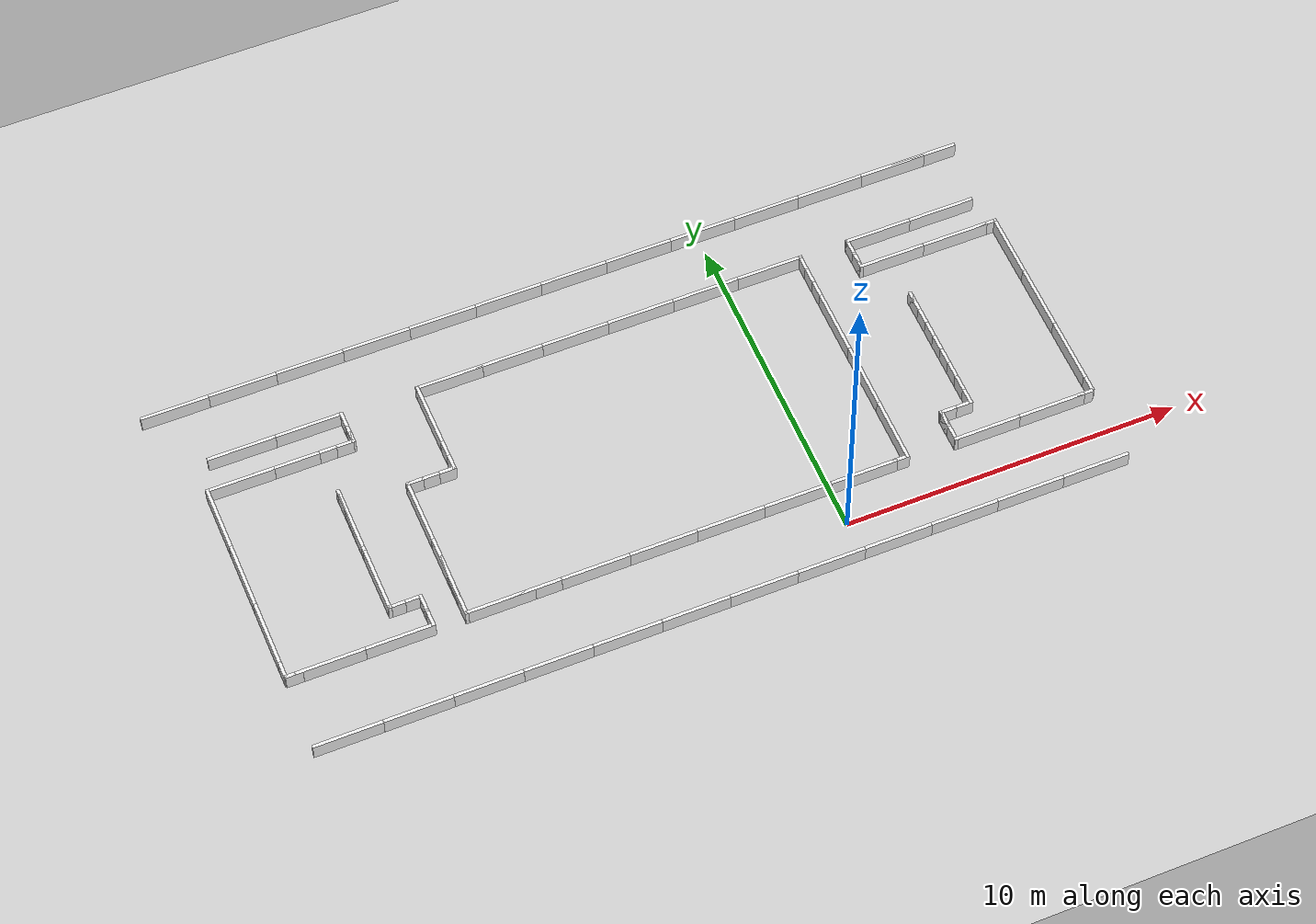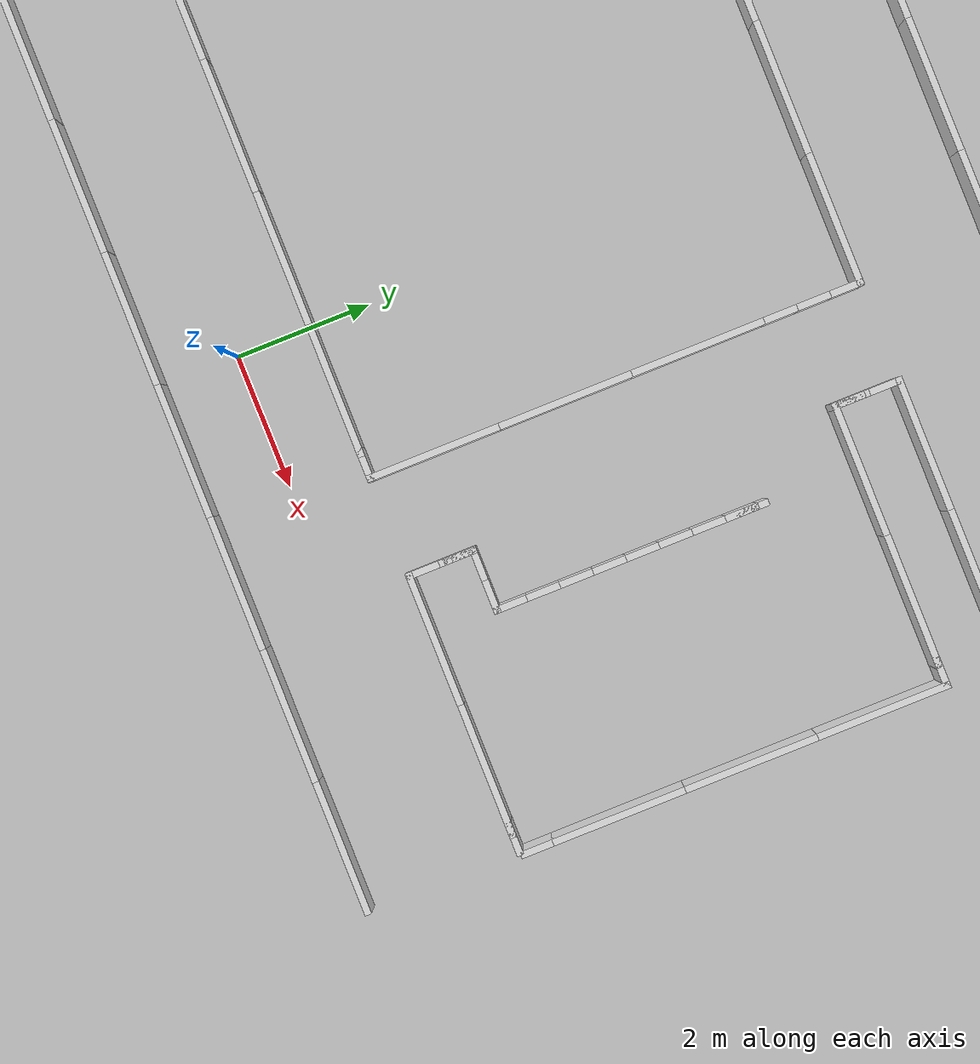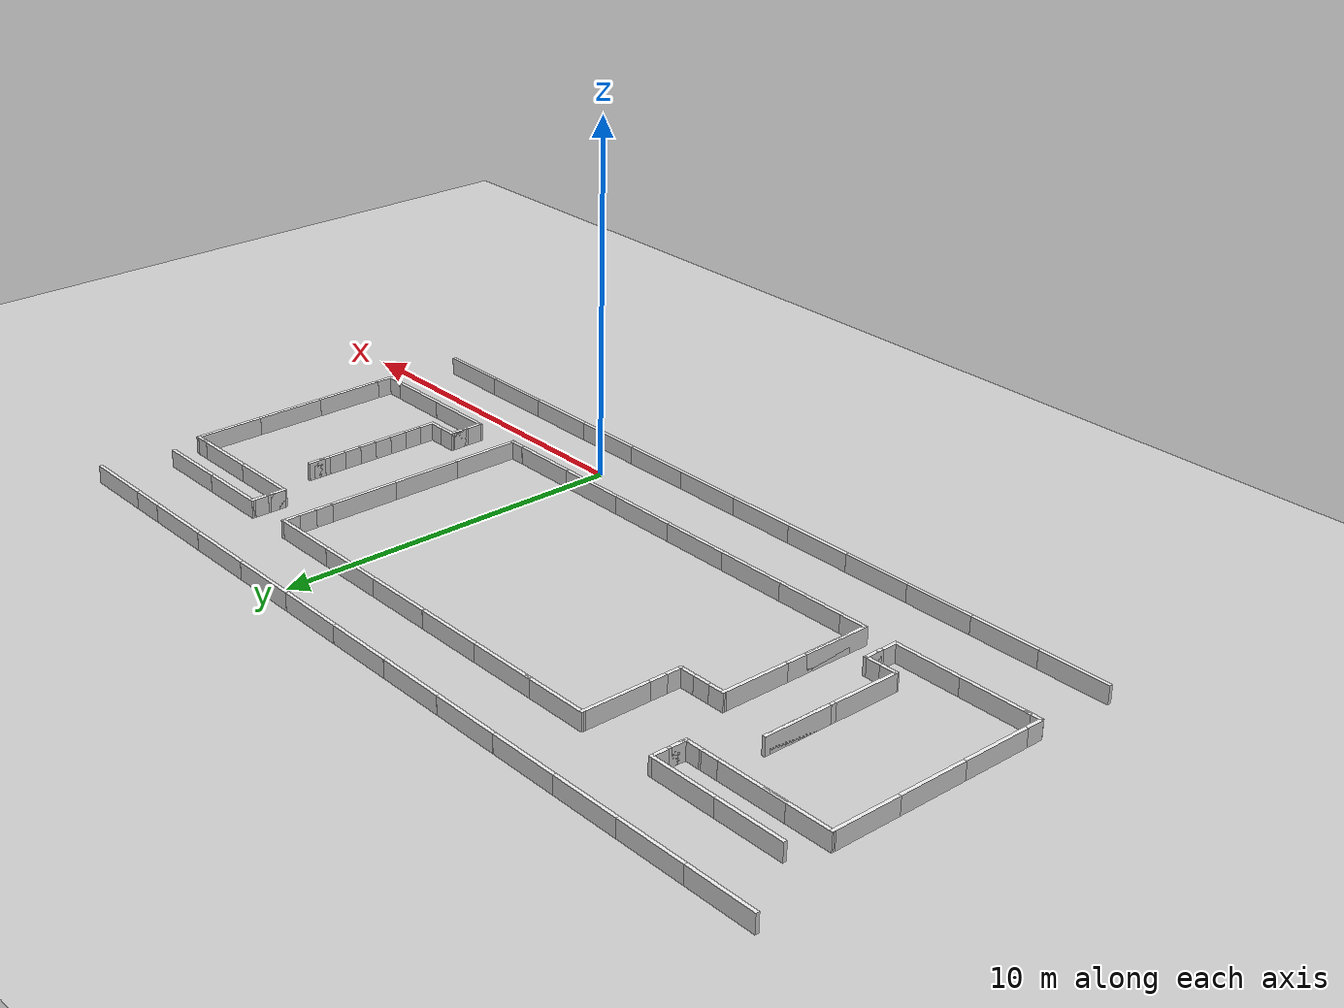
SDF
<?xml version="1.0" ?>
<!-- |    This document was autogenerated by xacro from /home/yuki/catkin_ws/src/raspimouse_sim/raspimouse_gazebo/materials/cit_bldg2_19f.world.xacro | -->
<!-- |    EDITING THIS FILE BY HAND IS NOT RECOMMENDED                                 | -->
<sdf version="1.4" xmlns:xacro="http://ros.org/wiki/xacro">
  <world name="default">
    <include>
      <uri>model://ground_plane</uri>
    </include>
    <light name="sun" type="directional">
      <cast_shadows>1</cast_shadows>
      <pose>0 0 5 0 0 0</pose>
      <diffuse>0.8 0.8 0.8 1</diffuse>
      <specular>0.2 0.2 0.2 1</specular>
      <attenuation>
        <range>1000</range>
        <constant>0.9</constant>
        <linear>0.01</linear>
        <quadratic>0.001</quadratic>
      </attenuation>
      <direction>-0.5 0.1 -0.9</direction>
    </light>
    <physics type="ode">
      <max_step_size>0.001</max_step_size>
      <real_time_factor>1</real_time_factor>
      <real_time_update_rate>1000</real_time_update_rate>
      <gravity>0 0 -9.8</gravity>
    </physics>
    <scene>
      <shadows>0</shadows>
    </scene>
    <gui fullscreen="0">
      <camera name="user_camera">
        <pose>-0.556842 -0.914575 1.68773 0 1.05964 0.520195</pose>
        <view_controller>orbit</view_controller>
      </camera>
    </gui>
    <model name="wall_corridor">
      <pose> -9.76 1.145 0.25 0 0 1.57</pose>
      <link name="link">
        <inertial>
          <mass>10</mass>
          <inertia>
            <ixx>1</ixx>
            <ixy>0</ixy>
            <ixz>0</ixz>
            <iyy>1</iyy>
            <iyz>0</iyz>
            <izz>1</izz>
          </inertia>
        </inertial>
        <collision name="collision">
          <geometry>
            <box>
              <size>0.1 2.0 0.5</size>
            </box>
          </geometry>
          <max_contacts>10</max_contacts>
          <surface>
            <bounce/>
            <friction>
              <ode/>
            </friction>
            <contact>
              <ode/>
            </contact>
          </surface>
        </collision>
        <visual name="visual">
          <geometry>
            <box>
              <size>0.1 2.0 0.5</size>
            </box>
          </geometry>
          <material>
            <script>
              <uri>file://media/materials/scripts/gazebo.material</uri>
              <name>Gazebo/White</name>
            </script>
          </material>
        </visual>
        <velocity_decay>
          <linear>0</linear>
          <angular>0</angular>
        </velocity_decay>
        <self_collide>0</self_collide>
        <kinematic>0</kinematic>
        <gravity>1</gravity>
      </link>
      <static>1</static>
    </model>
    <model name="wall_corridor">
      <pose> -9.0 1.145 0.25 0 0 1.57</pose>
      <link name="link">
        <inertial>
          <mass>10</mass>
          <inertia>
            <ixx>1</ixx>
            <ixy>0</ixy>
            <ixz>0</ixz>
            <iyy>1</iyy>
            <iyz>0</iyz>
            <izz>1</izz>
          </inertia>
        </inertial>
        <collision name="collision">
          <geometry>
            <box>
              <size>0.1 2.0 0.5</size>
            </box>
          </geometry>
          <max_contacts>10</max_contacts>
          <surface>
            <bounce/>
            <friction>
              <ode/>
            </friction>
            <contact>
              <ode/>
            </contact>
          </surface>
        </collision>
        <visual name="visual">
          <geometry>
            <box>
              <size>0.1 2.0 0.5</size>
            </box>
          </geometry>
          <material>
            <script>
              <uri>file://media/materials/scripts/gazebo.material</uri>
              <name>Gazebo/White</name>
            </script>
          </material>
        </visual>
        <velocity_decay>
          <linear>0</linear>
          <angular>0</angular>
        </velocity_decay>
        <self_collide>0</self_collide>
        <kinematic>0</kinematic>
        <gravity>1</gravity>
      </link>
      <static>1</static>
    </model>
    <model name="wall_corridor">
      <pose> -7.0 1.145 0.25 0 0 1.57</pose>
      <link name="link">
        <inertial>
          <mass>10</mass>
          <inertia>
            <ixx>1</ixx>
            <ixy>0</ixy>
            <ixz>0</ixz>
            <iyy>1</iyy>
            <iyz>0</iyz>
            <izz>1</izz>
          </inertia>
        </inertial>
        <collision name="collision">
          <geometry>
            <box>
              <size>0.1 2.0 0.5</size>
            </box>
          </geometry>
          <max_contacts>10</max_contacts>
          <surface>
            <bounce/>
            <friction>
              <ode/>
            </friction>
            <contact>
              <ode/>
            </contact>
          </surface>
        </collision>
        <visual name="visual">
          <geometry>
            <box>
              <size>0.1 2.0 0.5</size>
            </box>
          </geometry>
          <material>
            <script>
              <uri>file://media/materials/scripts/gazebo.material</uri>
              <name>Gazebo/White</name>
            </script>
          </material>
        </visual>
        <velocity_decay>
          <linear>0</linear>
          <angular>0</angular>
        </velocity_decay>
        <self_collide>0</self_collide>
        <kinematic>0</kinematic>
        <gravity>1</gravity>
      </link>
      <static>1</static>
    </model>
    <model name="wall_corridor">
      <pose> -5.0 1.145 0.25 0 0 1.57</pose>
      <link name="link">
        <inertial>
          <mass>10</mass>
          <inertia>
            <ixx>1</ixx>
            <ixy>0</ixy>
            <ixz>0</ixz>
            <iyy>1</iyy>
            <iyz>0</iyz>
            <izz>1</izz>
          </inertia>
        </inertial>
        <collision name="collision">
          <geometry>
            <box>
              <size>0.1 2.0 0.5</size>
            </box>
          </geometry>
          <max_contacts>10</max_contacts>
          <surface>
            <bounce/>
            <friction>
              <ode/>
            </friction>
            <contact>
              <ode/>
            </contact>
          </surface>
        </collision>
        <visual name="visual">
          <geometry>
            <box>
              <size>0.1 2.0 0.5</size>
            </box>
          </geometry>
          <material>
            <script>
              <uri>file://media/materials/scripts/gazebo.material</uri>
              <name>Gazebo/White</name>
            </script>
          </material>
        </visual>
        <velocity_decay>
          <linear>0</linear>
          <angular>0</angular>
        </velocity_decay>
        <self_collide>0</self_collide>
        <kinematic>0</kinematic>
        <gravity>1</gravity>
      </link>
      <static>1</static>
    </model>
    <model name="wall_corridor">
      <pose> -3.0 1.145 0.25 0 0 1.57</pose>
      <link name="link">
        <inertial>
          <mass>10</mass>
          <inertia>
            <ixx>1</ixx>
            <ixy>0</ixy>
            <ixz>0</ixz>
            <iyy>1</iyy>
            <iyz>0</iyz>
            <izz>1</izz>
          </inertia>
        </inertial>
        <collision name="collision">
          <geometry>
            <box>
              <size>0.1 2.0 0.5</size>
            </box>
          </geometry>
          <max_contacts>10</max_contacts>
          <surface>
            <bounce/>
            <friction>
              <ode/>
            </friction>
            <contact>
              <ode/>
            </contact>
          </surface>
        </collision>
        <visual name="visual">
          <geometry>
            <box>
              <size>0.1 2.0 0.5</size>
            </box>
          </geometry>
          <material>
            <script>
              <uri>file://media/materials/scripts/gazebo.material</uri>
              <name>Gazebo/White</name>
            </script>
          </material>
        </visual>
        <velocity_decay>
          <linear>0</linear>
          <angular>0</angular>
        </velocity_decay>
        <self_collide>0</self_collide>
        <kinematic>0</kinematic>
        <gravity>1</gravity>
      </link>
      <static>1</static>
    </model>
    <model name="wall_corridor">
      <pose> -1.0 1.145 0.25 0 0 1.57</pose>
      <link name="link">
        <inertial>
          <mass>10</mass>
          <inertia>
            <ixx>1</ixx>
            <ixy>0</ixy>
            <ixz>0</ixz>
            <iyy>1</iyy>
            <iyz>0</iyz>
            <izz>1</izz>
          </inertia>
        </inertial>
        <collision name="collision">
          <geometry>
            <box>
              <size>0.1 2.0 0.5</size>
            </box>
          </geometry>
          <max_contacts>10</max_contacts>
          <surface>
            <bounce/>
            <friction>
              <ode/>
            </friction>
            <contact>
              <ode/>
            </contact>
          </surface>
        </collision>
        <visual name="visual">
          <geometry>
            <box>
              <size>0.1 2.0 0.5</size>
            </box>
          </geometry>
          <material>
            <script>
              <uri>file://media/materials/scripts/gazebo.material</uri>
              <name>Gazebo/White</name>
            </script>
          </material>
        </visual>
        <velocity_decay>
          <linear>0</linear>
          <angular>0</angular>
        </velocity_decay>
        <self_collide>0</self_collide>
        <kinematic>0</kinematic>
        <gravity>1</gravity>
      </link>
      <static>1</static>
    </model>
    <model name="wall_corridor">
      <pose> 1.0 1.145 0.25 0 0 1.57</pose>
      <link name="link">
        <inertial>
          <mass>10</mass>
          <inertia>
            <ixx>1</ixx>
            <ixy>0</ixy>
            <ixz>0</ixz>
            <iyy>1</iyy>
            <iyz>0</iyz>
            <izz>1</izz>
          </inertia>
        </inertial>
        <collision name="collision">
          <geometry>
            <box>
              <size>0.1 2.0 0.5</size>
            </box>
          </geometry>
          <max_contacts>10</max_contacts>
          <surface>
            <bounce/>
            <friction>
              <ode/>
            </friction>
            <contact>
              <ode/>
            </contact>
          </surface>
        </collision>
        <visual name="visual">
          <geometry>
            <box>
              <size>0.1 2.0 0.5</size>
            </box>
          </geometry>
          <material>
            <script>
              <uri>file://media/materials/scripts/gazebo.material</uri>
              <name>Gazebo/White</name>
            </script>
          </material>
        </visual>
        <velocity_decay>
          <linear>0</linear>
          <angular>0</angular>
        </velocity_decay>
        <self_collide>0</self_collide>
        <kinematic>0</kinematic>
        <gravity>1</gravity>
      </link>
      <static>1</static>
    </model>
    <model name="wall">
      <pose> 2.12 1.145 0.25 0 0 1.57</pose>
      <link name="link">
        <inertial>
          <mass>10</mass>
          <inertia>
            <ixx>1</ixx>
            <ixy>0</ixy>
            <ixz>0</ixz>
            <iyy>1</iyy>
            <iyz>0</iyz>
            <izz>1</izz>
          </inertia>
        </inertial>
        <collision name="collision">
          <geometry>
            <box>
              <size>0.1 0.5 0.5</size>
            </box>
          </geometry>
          <max_contacts>10</max_contacts>
          <surface>
            <bounce/>
            <friction>
              <ode/>
            </friction>
            <contact>
              <ode/>
            </contact>
          </surface>
        </collision>
        <visual name="visual">
          <geometry>
            <box>
              <size>0.1 0.5 0.5</size>
            </box>
          </geometry>
          <material>
            <script>
              <uri>file://media/materials/scripts/gazebo.material</uri>
              <name>Gazebo/White</name>
            </script>
          </material>
        </visual>
        <velocity_decay>
          <linear>0</linear>
          <angular>0</angular>
        </velocity_decay>
        <self_collide>0</self_collide>
        <kinematic>0</kinematic>
        <gravity>1</gravity>
      </link>
      <static>1</static>
    </model>
    <model name="wall_corridor">
      <pose> 4.75 1.145 0.25 0 0 1.57</pose>
      <link name="link">
        <inertial>
          <mass>10</mass>
          <inertia>
            <ixx>1</ixx>
            <ixy>0</ixy>
            <ixz>0</ixz>
            <iyy>1</iyy>
            <iyz>0</iyz>
            <izz>1</izz>
          </inertia>
        </inertial>
        <collision name="collision">
          <geometry>
            <box>
              <size>0.1 2.0 0.5</size>
            </box>
          </geometry>
          <max_contacts>10</max_contacts>
          <surface>
            <bounce/>
            <friction>
              <ode/>
            </friction>
            <contact>
              <ode/>
            </contact>
          </surface>
        </collision>
        <visual name="visual">
          <geometry>
            <box>
              <size>0.1 2.0 0.5</size>
            </box>
          </geometry>
          <material>
            <script>
              <uri>file://media/materials/scripts/gazebo.material</uri>
              <name>Gazebo/White</name>
            </script>
          </material>
        </visual>
        <velocity_decay>
          <linear>0</linear>
          <angular>0</angular>
        </velocity_decay>
        <self_collide>0</self_collide>
        <kinematic>0</kinematic>
        <gravity>1</gravity>
      </link>
      <static>1</static>
    </model>
    <model name="wall_corridor">
      <pose> 6.75 1.145 0.25 0 0 1.57</pose>
      <link name="link">
        <inertial>
          <mass>10</mass>
          <inertia>
            <ixx>1</ixx>
            <ixy>0</ixy>
            <ixz>0</ixz>
            <iyy>1</iyy>
            <iyz>0</iyz>
            <izz>1</izz>
          </inertia>
        </inertial>
        <collision name="collision">
          <geometry>
            <box>
              <size>0.1 2.0 0.5</size>
            </box>
          </geometry>
          <max_contacts>10</max_contacts>
          <surface>
            <bounce/>
            <friction>
              <ode/>
            </friction>
            <contact>
              <ode/>
            </contact>
          </surface>
        </collision>
        <visual name="visual">
          <geometry>
            <box>
              <size>0.1 2.0 0.5</size>
            </box>
          </geometry>
          <material>
            <script>
              <uri>file://media/materials/scripts/gazebo.material</uri>
              <name>Gazebo/White</name>
            </script>
          </material>
        </visual>
        <velocity_decay>
          <linear>0</linear>
          <angular>0</angular>
        </velocity_decay>
        <self_collide>0</self_collide>
        <kinematic>0</kinematic>
        <gravity>1</gravity>
      </link>
      <static>1</static>
    </model>
    <model name="wall">
      <pose> 7.77 1.145 0.25 0 0 1.57</pose>
      <link name="link">
        <inertial>
          <mass>10</mass>
          <inertia>
            <ixx>1</ixx>
            <ixy>0</ixy>
            <ixz>0</ixz>
            <iyy>1</iyy>
            <iyz>0</iyz>
            <izz>1</izz>
          </inertia>
        </inertial>
        <collision name="collision">
          <geometry>
            <box>
              <size>0.1 0.5 0.5</size>
            </box>
          </geometry>
          <max_contacts>10</max_contacts>
          <surface>
            <bounce/>
            <friction>
              <ode/>
            </friction>
            <contact>
              <ode/>
            </contact>
          </surface>
        </collision>
        <visual name="visual">
          <geometry>
            <box>
              <size>0.1 0.5 0.5</size>
            </box>
          </geometry>
          <material>
            <script>
              <uri>file://media/materials/scripts/gazebo.material</uri>
              <name>Gazebo/White</name>
            </script>
          </material>
        </visual>
        <velocity_decay>
          <linear>0</linear>
          <angular>0</angular>
        </velocity_decay>
        <self_collide>0</self_collide>
        <kinematic>0</kinematic>
        <gravity>1</gravity>
      </link>
      <static>1</static>
    </model>
    <model name="wall_corridor">
      <pose> -15.0 -1.145 0.25 0 0 1.57</pose>
      <link name="link">
        <inertial>
          <mass>10</mass>
          <inertia>
            <ixx>1</ixx>
            <ixy>0</ixy>
            <ixz>0</ixz>
            <iyy>1</iyy>
            <iyz>0</iyz>
            <izz>1</izz>
          </inertia>
        </inertial>
        <collision name="collision">
          <geometry>
            <box>
              <size>0.1 2.0 0.5</size>
            </box>
          </geometry>
          <max_contacts>10</max_contacts>
          <surface>
            <bounce/>
            <friction>
              <ode/>
            </friction>
            <contact>
              <ode/>
            </contact>
          </surface>
        </collision>
        <visual name="visual">
          <geometry>
            <box>
              <size>0.1 2.0 0.5</size>
            </box>
          </geometry>
          <material>
            <script>
              <uri>file://media/materials/scripts/gazebo.material</uri>
              <name>Gazebo/White</name>
            </script>
          </material>
        </visual>
        <velocity_decay>
          <linear>0</linear>
          <angular>0</angular>
        </velocity_decay>
        <self_collide>0</self_collide>
        <kinematic>0</kinematic>
        <gravity>1</gravity>
      </link>
      <static>1</static>
    </model>
    <model name="wall_corridor">
      <pose> -13.0 -1.145 0.25 0 0 1.57</pose>
      <link name="link">
        <inertial>
          <mass>10</mass>
          <inertia>
            <ixx>1</ixx>
            <ixy>0</ixy>
            <ixz>0</ixz>
            <iyy>1</iyy>
            <iyz>0</iyz>
            <izz>1</izz>
          </inertia>
        </inertial>
        <collision name="collision">
          <geometry>
            <box>
              <size>0.1 2.0 0.5</size>
            </box>
          </geometry>
          <max_contacts>10</max_contacts>
          <surface>
            <bounce/>
            <friction>
              <ode/>
            </friction>
            <contact>
              <ode/>
            </contact>
          </surface>
        </collision>
        <visual name="visual">
          <geometry>
            <box>
              <size>0.1 2.0 0.5</size>
            </box>
          </geometry>
          <material>
            <script>
              <uri>file://media/materials/scripts/gazebo.material</uri>
              <name>Gazebo/White</name>
            </script>
          </material>
        </visual>
        <velocity_decay>
          <linear>0</linear>
          <angular>0</angular>
        </velocity_decay>
        <self_collide>0</self_collide>
        <kinematic>0</kinematic>
        <gravity>1</gravity>
      </link>
      <static>1</static>
    </model>
    <model name="wall_corridor">
      <pose> -11.0 -1.145 0.25 0 0 1.57</pose>
      <link name="link">
        <inertial>
          <mass>10</mass>
          <inertia>
            <ixx>1</ixx>
            <ixy>0</ixy>
            <ixz>0</ixz>
            <iyy>1</iyy>
            <iyz>0</iyz>
            <izz>1</izz>
          </inertia>
        </inertial>
        <collision name="collision">
          <geometry>
            <box>
              <size>0.1 2.0 0.5</size>
            </box>
          </geometry>
          <max_contacts>10</max_contacts>
          <surface>
            <bounce/>
            <friction>
              <ode/>
            </friction>
            <contact>
              <ode/>
            </contact>
          </surface>
        </collision>
        <visual name="visual">
          <geometry>
            <box>
              <size>0.1 2.0 0.5</size>
            </box>
          </geometry>
          <material>
            <script>
              <uri>file://media/materials/scripts/gazebo.material</uri>
              <name>Gazebo/White</name>
            </script>
          </material>
        </visual>
        <velocity_decay>
          <linear>0</linear>
          <angular>0</angular>
        </velocity_decay>
        <self_collide>0</self_collide>
        <kinematic>0</kinematic>
        <gravity>1</gravity>
      </link>
      <static>1</static>
    </model>
    <model name="wall_corridor">
      <pose> -9.0 -1.145 0.25 0 0 1.57</pose>
      <link name="link">
        <inertial>
          <mass>10</mass>
          <inertia>
            <ixx>1</ixx>
            <ixy>0</ixy>
            <ixz>0</ixz>
            <iyy>1</iyy>
            <iyz>0</iyz>
            <izz>1</izz>
          </inertia>
        </inertial>
        <collision name="collision">
          <geometry>
            <box>
              <size>0.1 2.0 0.5</size>
            </box>
          </geometry>
          <max_contacts>10</max_contacts>
          <surface>
            <bounce/>
            <friction>
              <ode/>
            </friction>
            <contact>
              <ode/>
            </contact>
          </surface>
        </collision>
        <visual name="visual">
          <geometry>
            <box>
              <size>0.1 2.0 0.5</size>
            </box>
          </geometry>
          <material>
            <script>
              <uri>file://media/materials/scripts/gazebo.material</uri>
              <name>Gazebo/White</name>
            </script>
          </material>
        </visual>
        <velocity_decay>
          <linear>0</linear>
          <angular>0</angular>
        </velocity_decay>
        <self_collide>0</self_collide>
        <kinematic>0</kinematic>
        <gravity>1</gravity>
      </link>
      <static>1</static>
    </model>
    <model name="wall_corridor">
      <pose> -7.0 -1.145 0.25 0 0 1.57</pose>
      <link name="link">
        <inertial>
          <mass>10</mass>
          <inertia>
            <ixx>1</ixx>
            <ixy>0</ixy>
            <ixz>0</ixz>
            <iyy>1</iyy>
            <iyz>0</iyz>
            <izz>1</izz>
          </inertia>
        </inertial>
        <collision name="collision">
          <geometry>
            <box>
              <size>0.1 2.0 0.5</size>
            </box>
          </geometry>
          <max_contacts>10</max_contacts>
          <surface>
            <bounce/>
            <friction>
              <ode/>
            </friction>
            <contact>
              <ode/>
            </contact>
          </surface>
        </collision>
        <visual name="visual">
          <geometry>
            <box>
              <size>0.1 2.0 0.5</size>
            </box>
          </geometry>
          <material>
            <script>
              <uri>file://media/materials/scripts/gazebo.material</uri>
              <name>Gazebo/White</name>
            </script>
          </material>
        </visual>
        <velocity_decay>
          <linear>0</linear>
          <angular>0</angular>
        </velocity_decay>
        <self_collide>0</self_collide>
        <kinematic>0</kinematic>
        <gravity>1</gravity>
      </link>
      <static>1</static>
    </model>
    <model name="wall_corridor">
      <pose> -5.0 -1.145 0.25 0 0 1.57</pose>
      <link name="link">
        <inertial>
          <mass>10</mass>
          <inertia>
            <ixx>1</ixx>
            <ixy>0</ixy>
            <ixz>0</ixz>
            <iyy>1</iyy>
            <iyz>0</iyz>
            <izz>1</izz>
          </inertia>
        </inertial>
        <collision name="collision">
          <geometry>
            <box>
              <size>0.1 2.0 0.5</size>
            </box>
          </geometry>
          <max_contacts>10</max_contacts>
          <surface>
            <bounce/>
            <friction>
              <ode/>
            </friction>
            <contact>
              <ode/>
            </contact>
          </surface>
        </collision>
        <visual name="visual">
          <geometry>
            <box>
              <size>0.1 2.0 0.5</size>
            </box>
          </geometry>
          <material>
            <script>
              <uri>file://media/materials/scripts/gazebo.material</uri>
              <name>Gazebo/White</name>
            </script>
          </material>
        </visual>
        <velocity_decay>
          <linear>0</linear>
          <angular>0</angular>
        </velocity_decay>
        <self_collide>0</self_collide>
        <kinematic>0</kinematic>
        <gravity>1</gravity>
      </link>
      <static>1</static>
    </model>
    <model name="wall_corridor">
      <pose> -3.0 -1.145 0.25 0 0 1.57</pose>
      <link name="link">
        <inertial>
          <mass>10</mass>
          <inertia>
            <ixx>1</ixx>
            <ixy>0</ixy>
            <ixz>0</ixz>
            <iyy>1</iyy>
            <iyz>0</iyz>
            <izz>1</izz>
          </inertia>
        </inertial>
        <collision name="collision">
          <geometry>
            <box>
              <size>0.1 2.0 0.5</size>
            </box>
          </geometry>
          <max_contacts>10</max_contacts>
          <surface>
            <bounce/>
            <friction>
              <ode/>
            </friction>
            <contact>
              <ode/>
            </contact>
          </surface>
        </collision>
        <visual name="visual">
          <geometry>
            <box>
              <size>0.1 2.0 0.5</size>
            </box>
          </geometry>
          <material>
            <script>
              <uri>file://media/materials/scripts/gazebo.material</uri>
              <name>Gazebo/White</name>
            </script>
          </material>
        </visual>
        <velocity_decay>
          <linear>0</linear>
          <angular>0</angular>
        </velocity_decay>
        <self_collide>0</self_collide>
        <kinematic>0</kinematic>
        <gravity>1</gravity>
      </link>
      <static>1</static>
    </model>
    <model name="wall_corridor">
      <pose> -1.0 -1.145 0.25 0 0 1.57</pose>
      <link name="link">
        <inertial>
          <mass>10</mass>
          <inertia>
            <ixx>1</ixx>
            <ixy>0</ixy>
            <ixz>0</ixz>
            <iyy>1</iyy>
            <iyz>0</iyz>
            <izz>1</izz>
          </inertia>
        </inertial>
        <collision name="collision">
          <geometry>
            <box>
              <size>0.1 2.0 0.5</size>
            </box>
          </geometry>
          <max_contacts>10</max_contacts>
          <surface>
            <bounce/>
            <friction>
              <ode/>
            </friction>
            <contact>
              <ode/>
            </contact>
          </surface>
        </collision>
        <visual name="visual">
          <geometry>
            <box>
              <size>0.1 2.0 0.5</size>
            </box>
          </geometry>
          <material>
            <script>
              <uri>file://media/materials/scripts/gazebo.material</uri>
              <name>Gazebo/White</name>
            </script>
          </material>
        </visual>
        <velocity_decay>
          <linear>0</linear>
          <angular>0</angular>
        </velocity_decay>
        <self_collide>0</self_collide>
        <kinematic>0</kinematic>
        <gravity>1</gravity>
      </link>
      <static>1</static>
    </model>
    <model name="wall_corridor">
      <pose> 1.0 -1.1455 0.25 0 0 1.57</pose>
      <link name="link">
        <inertial>
          <mass>10</mass>
          <inertia>
            <ixx>1</ixx>
            <ixy>0</ixy>
            <ixz>0</ixz>
            <iyy>1</iyy>
            <iyz>0</iyz>
            <izz>1</izz>
          </inertia>
        </inertial>
        <collision name="collision">
          <geometry>
            <box>
              <size>0.1 2.0 0.5</size>
            </box>
          </geometry>
          <max_contacts>10</max_contacts>
          <surface>
            <bounce/>
            <friction>
              <ode/>
            </friction>
            <contact>
              <ode/>
            </contact>
          </surface>
        </collision>
        <visual name="visual">
          <geometry>
            <box>
              <size>0.1 2.0 0.5</size>
            </box>
          </geometry>
          <material>
            <script>
              <uri>file://media/materials/scripts/gazebo.material</uri>
              <name>Gazebo/White</name>
            </script>
          </material>
        </visual>
        <velocity_decay>
          <linear>0</linear>
          <angular>0</angular>
        </velocity_decay>
        <self_collide>0</self_collide>
        <kinematic>0</kinematic>
        <gravity>1</gravity>
      </link>
      <static>1</static>
    </model>
    <model name="wall_corridor">
      <pose> 3.0 -1.145 0.25 0 0 1.57</pose>
      <link name="link">
        <inertial>
          <mass>10</mass>
          <inertia>
            <ixx>1</ixx>
            <ixy>0</ixy>
            <ixz>0</ixz>
            <iyy>1</iyy>
            <iyz>0</iyz>
            <izz>1</izz>
          </inertia>
        </inertial>
        <collision name="collision">
          <geometry>
            <box>
              <size>0.1 2.0 0.5</size>
            </box>
          </geometry>
          <max_contacts>10</max_contacts>
          <surface>
            <bounce/>
            <friction>
              <ode/>
            </friction>
            <contact>
              <ode/>
            </contact>
          </surface>
        </collision>
        <visual name="visual">
          <geometry>
            <box>
              <size>0.1 2.0 0.5</size>
            </box>
          </geometry>
          <material>
            <script>
              <uri>file://media/materials/scripts/gazebo.material</uri>
              <name>Gazebo/White</name>
            </script>
          </material>
        </visual>
        <velocity_decay>
          <linear>0</linear>
          <angular>0</angular>
        </velocity_decay>
        <self_collide>0</self_collide>
        <kinematic>0</kinematic>
        <gravity>1</gravity>
      </link>
      <static>1</static>
    </model>
    <model name="wall_corridor">
      <pose> 5.0 -1.145 0.25 0 0 1.57</pose>
      <link name="link">
        <inertial>
          <mass>10</mass>
          <inertia>
            <ixx>1</ixx>
            <ixy>0</ixy>
            <ixz>0</ixz>
            <iyy>1</iyy>
            <iyz>0</iyz>
            <izz>1</izz>
          </inertia>
        </inertial>
        <collision name="collision">
          <geometry>
            <box>
              <size>0.1 2.0 0.5</size>
            </box>
          </geometry>
          <max_contacts>10</max_contacts>
          <surface>
            <bounce/>
            <friction>
              <ode/>
            </friction>
            <contact>
              <ode/>
            </contact>
          </surface>
        </collision>
        <visual name="visual">
          <geometry>
            <box>
              <size>0.1 2.0 0.5</size>
            </box>
          </geometry>
          <material>
            <script>
              <uri>file://media/materials/scripts/gazebo.material</uri>
              <name>Gazebo/White</name>
            </script>
          </material>
        </visual>
        <velocity_decay>
          <linear>0</linear>
          <angular>0</angular>
        </velocity_decay>
        <self_collide>0</self_collide>
        <kinematic>0</kinematic>
        <gravity>1</gravity>
      </link>
      <static>1</static>
    </model>
    <model name="wall_corridor">
      <pose> 7.0 -1.145 0.25 0 0 1.57</pose>
      <link name="link">
        <inertial>
          <mass>10</mass>
          <inertia>
            <ixx>1</ixx>
            <ixy>0</ixy>
            <ixz>0</ixz>
            <iyy>1</iyy>
            <iyz>0</iyz>
            <izz>1</izz>
          </inertia>
        </inertial>
        <collision name="collision">
          <geometry>
            <box>
              <size>0.1 2.0 0.5</size>
            </box>
          </geometry>
          <max_contacts>10</max_contacts>
          <surface>
            <bounce/>
            <friction>
              <ode/>
            </friction>
            <contact>
              <ode/>
            </contact>
          </surface>
        </collision>
        <visual name="visual">
          <geometry>
            <box>
              <size>0.1 2.0 0.5</size>
            </box>
          </geometry>
          <material>
            <script>
              <uri>file://media/materials/scripts/gazebo.material</uri>
              <name>Gazebo/White</name>
            </script>
          </material>
        </visual>
        <velocity_decay>
          <linear>0</linear>
          <angular>0</angular>
        </velocity_decay>
        <self_collide>0</self_collide>
        <kinematic>0</kinematic>
        <gravity>1</gravity>
      </link>
      <static>1</static>
    </model>
    <model name="wall_corridor">
      <pose> 2.32 2.095 0.25 0 0 0</pose>
      <link name="link">
        <inertial>
          <mass>10</mass>
          <inertia>
            <ixx>1</ixx>
            <ixy>0</ixy>
            <ixz>0</ixz>
            <iyy>1</iyy>
            <iyz>0</iyz>
            <izz>1</izz>
          </inertia>
        </inertial>
        <collision name="collision">
          <geometry>
            <box>
              <size>0.1 2.0 0.5</size>
            </box>
          </geometry>
          <max_contacts>10</max_contacts>
          <surface>
            <bounce/>
            <friction>
              <ode/>
            </friction>
            <contact>
              <ode/>
            </contact>
          </surface>
        </collision>
        <visual name="visual">
          <geometry>
            <box>
              <size>0.1 2.0 0.5</size>
            </box>
          </geometry>
          <material>
            <script>
              <uri>file://media/materials/scripts/gazebo.material</uri>
              <name>Gazebo/White</name>
            </script>
          </material>
        </visual>
        <velocity_decay>
          <linear>0</linear>
          <angular>0</angular>
        </velocity_decay>
        <self_collide>0</self_collide>
        <kinematic>0</kinematic>
        <gravity>1</gravity>
      </link>
      <static>1</static>
    </model>
    <model name="wall_corridor">
      <pose> 2.32 4.095 0.25 0 0 0</pose>
      <link name="link">
        <inertial>
          <mass>10</mass>
          <inertia>
            <ixx>1</ixx>
            <ixy>0</ixy>
            <ixz>0</ixz>
            <iyy>1</iyy>
            <iyz>0</iyz>
            <izz>1</izz>
          </inertia>
        </inertial>
        <collision name="collision">
          <geometry>
            <box>
              <size>0.1 2.0 0.5</size>
            </box>
          </geometry>
          <max_contacts>10</max_contacts>
          <surface>
            <bounce/>
            <friction>
              <ode/>
            </friction>
            <contact>
              <ode/>
            </contact>
          </surface>
        </collision>
        <visual name="visual">
          <geometry>
            <box>
              <size>0.1 2.0 0.5</size>
            </box>
          </geometry>
          <material>
            <script>
              <uri>file://media/materials/scripts/gazebo.material</uri>
              <name>Gazebo/White</name>
            </script>
          </material>
        </visual>
        <velocity_decay>
          <linear>0</linear>
          <angular>0</angular>
        </velocity_decay>
        <self_collide>0</self_collide>
        <kinematic>0</kinematic>
        <gravity>1</gravity>
      </link>
      <static>1</static>
    </model>
    <model name="wall_corridor">
      <pose> 2.32 6.095 0.25 0 0 0</pose>
      <link name="link">
        <inertial>
          <mass>10</mass>
          <inertia>
            <ixx>1</ixx>
            <ixy>0</ixy>
            <ixz>0</ixz>
            <iyy>1</iyy>
            <iyz>0</iyz>
            <izz>1</izz>
          </inertia>
        </inertial>
        <collision name="collision">
          <geometry>
            <box>
              <size>0.1 2.0 0.5</size>
            </box>
          </geometry>
          <max_contacts>10</max_contacts>
          <surface>
            <bounce/>
            <friction>
              <ode/>
            </friction>
            <contact>
              <ode/>
            </contact>
          </surface>
        </collision>
        <visual name="visual">
          <geometry>
            <box>
              <size>0.1 2.0 0.5</size>
            </box>
          </geometry>
          <material>
            <script>
              <uri>file://media/materials/scripts/gazebo.material</uri>
              <name>Gazebo/White</name>
            </script>
          </material>
        </visual>
        <velocity_decay>
          <linear>0</linear>
          <angular>0</angular>
        </velocity_decay>
        <self_collide>0</self_collide>
        <kinematic>0</kinematic>
        <gravity>1</gravity>
      </link>
      <static>1</static>
    </model>
    <model name="wall">
      <pose> 2.32 7.345 0.25 0 0 0</pose>
      <link name="link">
        <inertial>
          <mass>10</mass>
          <inertia>
            <ixx>1</ixx>
            <ixy>0</ixy>
            <ixz>0</ixz>
            <iyy>1</iyy>
            <iyz>0</iyz>
            <izz>1</izz>
          </inertia>
        </inertial>
        <collision name="collision">
          <geometry>
            <box>
              <size>0.1 0.5 0.5</size>
            </box>
          </geometry>
          <max_contacts>10</max_contacts>
          <surface>
            <bounce/>
            <friction>
              <ode/>
            </friction>
            <contact>
              <ode/>
            </contact>
          </surface>
        </collision>
        <visual name="visual">
          <geometry>
            <box>
              <size>0.1 0.5 0.5</size>
            </box>
          </geometry>
          <material>
            <script>
              <uri>file://media/materials/scripts/gazebo.material</uri>
              <name>Gazebo/White</name>
            </script>
          </material>
        </visual>
        <velocity_decay>
          <linear>0</linear>
          <angular>0</angular>
        </velocity_decay>
        <self_collide>0</self_collide>
        <kinematic>0</kinematic>
        <gravity>1</gravity>
      </link>
      <static>1</static>
    </model>
    <model name="wall">
      <pose> 2.32 7.845 0.25 0 0 0</pose>
      <link name="link">
        <inertial>
          <mass>10</mass>
          <inertia>
            <ixx>1</ixx>
            <ixy>0</ixy>
            <ixz>0</ixz>
            <iyy>1</iyy>
            <iyz>0</iyz>
            <izz>1</izz>
          </inertia>
        </inertial>
        <collision name="collision">
          <geometry>
            <box>
              <size>0.1 0.5 0.5</size>
            </box>
          </geometry>
          <max_contacts>10</max_contacts>
          <surface>
            <bounce/>
            <friction>
              <ode/>
            </friction>
            <contact>
              <ode/>
            </contact>
          </surface>
        </collision>
        <visual name="visual">
          <geometry>
            <box>
              <size>0.1 0.5 0.5</size>
            </box>
          </geometry>
          <material>
            <script>
              <uri>file://media/materials/scripts/gazebo.material</uri>
              <name>Gazebo/White</name>
            </script>
          </material>
        </visual>
        <velocity_decay>
          <linear>0</linear>
          <angular>0</angular>
        </velocity_decay>
        <self_collide>0</self_collide>
        <kinematic>0</kinematic>
        <gravity>1</gravity>
      </link>
      <static>1</static>
    </model>
    <model name="wall">
      <pose> 2.32 8.345 0.25 0 0 0</pose>
      <link name="link">
        <inertial>
          <mass>10</mass>
          <inertia>
            <ixx>1</ixx>
            <ixy>0</ixy>
            <ixz>0</ixz>
            <iyy>1</iyy>
            <iyz>0</iyz>
            <izz>1</izz>
          </inertia>
        </inertial>
        <collision name="collision">
          <geometry>
            <box>
              <size>0.1 0.5 0.5</size>
            </box>
          </geometry>
          <max_contacts>10</max_contacts>
          <surface>
            <bounce/>
            <friction>
              <ode/>
            </friction>
            <contact>
              <ode/>
            </contact>
          </surface>
        </collision>
        <visual name="visual">
          <geometry>
            <box>
              <size>0.1 0.5 0.5</size>
            </box>
          </geometry>
          <material>
            <script>
              <uri>file://media/materials/scripts/gazebo.material</uri>
              <name>Gazebo/White</name>
            </script>
          </material>
        </visual>
        <velocity_decay>
          <linear>0</linear>
          <angular>0</angular>
        </velocity_decay>
        <self_collide>0</self_collide>
        <kinematic>0</kinematic>
        <gravity>1</gravity>
      </link>
      <static>1</static>
    </model>
    <model name="wall">
      <pose> 3.8 1.345 0.25 0 0 0</pose>
      <link name="link">
        <inertial>
          <mass>10</mass>
          <inertia>
            <ixx>1</ixx>
            <ixy>0</ixy>
            <ixz>0</ixz>
            <iyy>1</iyy>
            <iyz>0</iyz>
            <izz>1</izz>
          </inertia>
        </inertial>
        <collision name="collision">
          <geometry>
            <box>
              <size>0.1 0.5 0.5</size>
            </box>
          </geometry>
          <max_contacts>10</max_contacts>
          <surface>
            <bounce/>
            <friction>
              <ode/>
            </friction>
            <contact>
              <ode/>
            </contact>
          </surface>
        </collision>
        <visual name="visual">
          <geometry>
            <box>
              <size>0.1 0.5 0.5</size>
            </box>
          </geometry>
          <material>
            <script>
              <uri>file://media/materials/scripts/gazebo.material</uri>
              <name>Gazebo/White</name>
            </script>
          </material>
        </visual>
        <velocity_decay>
          <linear>0</linear>
          <angular>0</angular>
        </velocity_decay>
        <self_collide>0</self_collide>
        <kinematic>0</kinematic>
        <gravity>1</gravity>
      </link>
      <static>1</static>
    </model>
    <model name="wall">
      <pose> 3.8 1.845 0.25 0 0 0</pose>
      <link name="link">
        <inertial>
          <mass>10</mass>
          <inertia>
            <ixx>1</ixx>
            <ixy>0</ixy>
            <ixz>0</ixz>
            <iyy>1</iyy>
            <iyz>0</iyz>
            <izz>1</izz>
          </inertia>
        </inertial>
        <collision name="collision">
          <geometry>
            <box>
              <size>0.1 0.5 0.5</size>
            </box>
          </geometry>
          <max_contacts>10</max_contacts>
          <surface>
            <bounce/>
            <friction>
              <ode/>
            </friction>
            <contact>
              <ode/>
            </contact>
          </surface>
        </collision>
        <visual name="visual">
          <geometry>
            <box>
              <size>0.1 0.5 0.5</size>
            </box>
          </geometry>
          <material>
            <script>
              <uri>file://media/materials/scripts/gazebo.material</uri>
              <name>Gazebo/White</name>
            </script>
          </material>
        </visual>
        <velocity_decay>
          <linear>0</linear>
          <angular>0</angular>
        </velocity_decay>
        <self_collide>0</self_collide>
        <kinematic>0</kinematic>
        <gravity>1</gravity>
      </link>
      <static>1</static>
    </model>
    <model name="wall">
      <pose> 3.8 1.91 0.25 0 0 0</pose>
      <link name="link">
        <inertial>
          <mass>10</mass>
          <inertia>
            <ixx>1</ixx>
            <ixy>0</ixy>
            <ixz>0</ixz>
            <iyy>1</iyy>
            <iyz>0</iyz>
            <izz>1</izz>
          </inertia>
        </inertial>
        <collision name="collision">
          <geometry>
            <box>
              <size>0.1 0.5 0.5</size>
            </box>
          </geometry>
          <max_contacts>10</max_contacts>
          <surface>
            <bounce/>
            <friction>
              <ode/>
            </friction>
            <contact>
              <ode/>
            </contact>
          </surface>
        </collision>
        <visual name="visual">
          <geometry>
            <box>
              <size>0.1 0.5 0.5</size>
            </box>
          </geometry>
          <material>
            <script>
              <uri>file://media/materials/scripts/gazebo.material</uri>
              <name>Gazebo/White</name>
            </script>
          </material>
        </visual>
        <velocity_decay>
          <linear>0</linear>
          <angular>0</angular>
        </velocity_decay>
        <self_collide>0</self_collide>
        <kinematic>0</kinematic>
        <gravity>1</gravity>
      </link>
      <static>1</static>
    </model>
    <model name="wall">
      <pose> 4.0 2.11 0.25 0 0 1.57</pose>
      <link name="link">
        <inertial>
          <mass>10</mass>
          <inertia>
            <ixx>1</ixx>
            <ixy>0</ixy>
            <ixz>0</ixz>
            <iyy>1</iyy>
            <iyz>0</iyz>
            <izz>1</izz>
          </inertia>
        </inertial>
        <collision name="collision">
          <geometry>
            <box>
              <size>0.1 0.5 0.5</size>
            </box>
          </geometry>
          <max_contacts>10</max_contacts>
          <surface>
            <bounce/>
            <friction>
              <ode/>
            </friction>
            <contact>
              <ode/>
            </contact>
          </surface>
        </collision>
        <visual name="visual">
          <geometry>
            <box>
              <size>0.1 0.5 0.5</size>
            </box>
          </geometry>
          <material>
            <script>
              <uri>file://media/materials/scripts/gazebo.material</uri>
              <name>Gazebo/White</name>
            </script>
          </material>
        </visual>
        <velocity_decay>
          <linear>0</linear>
          <angular>0</angular>
        </velocity_decay>
        <self_collide>0</self_collide>
        <kinematic>0</kinematic>
        <gravity>1</gravity>
      </link>
      <static>1</static>
    </model>
    <model name="wall">
      <pose> 4.5 2.11 0.25 0 0 1.57</pose>
      <link name="link">
        <inertial>
          <mass>10</mass>
          <inertia>
            <ixx>1</ixx>
            <ixy>0</ixy>
            <ixz>0</ixz>
            <iyy>1</iyy>
            <iyz>0</iyz>
            <izz>1</izz>
          </inertia>
        </inertial>
        <collision name="collision">
          <geometry>
            <box>
              <size>0.1 0.5 0.5</size>
            </box>
          </geometry>
          <max_contacts>10</max_contacts>
          <surface>
            <bounce/>
            <friction>
              <ode/>
            </friction>
            <contact>
              <ode/>
            </contact>
          </surface>
        </collision>
        <visual name="visual">
          <geometry>
            <box>
              <size>0.1 0.5 0.5</size>
            </box>
          </geometry>
          <material>
            <script>
              <uri>file://media/materials/scripts/gazebo.material</uri>
              <name>Gazebo/White</name>
            </script>
          </material>
        </visual>
        <velocity_decay>
          <linear>0</linear>
          <angular>0</angular>
        </velocity_decay>
        <self_collide>0</self_collide>
        <kinematic>0</kinematic>
        <gravity>1</gravity>
      </link>
      <static>1</static>
    </model>
    <model name="wall">
      <pose> 4.7 2.31 0.25 0 0 0</pose>
      <link name="link">
        <inertial>
          <mass>10</mass>
          <inertia>
            <ixx>1</ixx>
            <ixy>0</ixy>
            <ixz>0</ixz>
            <iyy>1</iyy>
            <iyz>0</iyz>
            <izz>1</izz>
          </inertia>
        </inertial>
        <collision name="collision">
          <geometry>
            <box>
              <size>0.1 0.5 0.5</size>
            </box>
          </geometry>
          <max_contacts>10</max_contacts>
          <surface>
            <bounce/>
            <friction>
              <ode/>
            </friction>
            <contact>
              <ode/>
            </contact>
          </surface>
        </collision>
        <visual name="visual">
          <geometry>
            <box>
              <size>0.1 0.5 0.5</size>
            </box>
          </geometry>
          <material>
            <script>
              <uri>file://media/materials/scripts/gazebo.material</uri>
              <name>Gazebo/White</name>
            </script>
          </material>
        </visual>
        <velocity_decay>
          <linear>0</linear>
          <angular>0</angular>
        </velocity_decay>
        <self_collide>0</self_collide>
        <kinematic>0</kinematic>
        <gravity>1</gravity>
      </link>
      <static>1</static>
    </model>
    <model name="wall">
      <pose> 4.7 2.81 0.25 0 0 0</pose>
      <link name="link">
        <inertial>
          <mass>10</mass>
          <inertia>
            <ixx>1</ixx>
            <ixy>0</ixy>
            <ixz>0</ixz>
            <iyy>1</iyy>
            <iyz>0</iyz>
            <izz>1</izz>
          </inertia>
        </inertial>
        <collision name="collision">
          <geometry>
            <box>
              <size>0.1 0.5 0.5</size>
            </box>
          </geometry>
          <max_contacts>10</max_contacts>
          <surface>
            <bounce/>
            <friction>
              <ode/>
            </friction>
            <contact>
              <ode/>
            </contact>
          </surface>
        </collision>
        <visual name="visual">
          <geometry>
            <box>
              <size>0.1 0.5 0.5</size>
            </box>
          </geometry>
          <material>
            <script>
              <uri>file://media/materials/scripts/gazebo.material</uri>
              <name>Gazebo/White</name>
            </script>
          </material>
        </visual>
        <velocity_decay>
          <linear>0</linear>
          <angular>0</angular>
        </velocity_decay>
        <self_collide>0</self_collide>
        <kinematic>0</kinematic>
        <gravity>1</gravity>
      </link>
      <static>1</static>
    </model>
    <model name="wall">
      <pose> 4.7 3.31 0.25 0 0 0</pose>
      <link name="link">
        <inertial>
          <mass>10</mass>
          <inertia>
            <ixx>1</ixx>
            <ixy>0</ixy>
            <ixz>0</ixz>
            <iyy>1</iyy>
            <iyz>0</iyz>
            <izz>1</izz>
          </inertia>
        </inertial>
        <collision name="collision">
          <geometry>
            <box>
              <size>0.1 0.5 0.5</size>
            </box>
          </geometry>
          <max_contacts>10</max_contacts>
          <surface>
            <bounce/>
            <friction>
              <ode/>
            </friction>
            <contact>
              <ode/>
            </contact>
          </surface>
        </collision>
        <visual name="visual">
          <geometry>
            <box>
              <size>0.1 0.5 0.5</size>
            </box>
          </geometry>
          <material>
            <script>
              <uri>file://media/materials/scripts/gazebo.material</uri>
              <name>Gazebo/White</name>
            </script>
          </material>
        </visual>
        <velocity_decay>
          <linear>0</linear>
          <angular>0</angular>
        </velocity_decay>
        <self_collide>0</self_collide>
        <kinematic>0</kinematic>
        <gravity>1</gravity>
      </link>
      <static>1</static>
    </model>
    <model name="wall">
      <pose> 4.7 3.81 0.25 0 0 0</pose>
      <link name="link">
        <inertial>
          <mass>10</mass>
          <inertia>
            <ixx>1</ixx>
            <ixy>0</ixy>
            <ixz>0</ixz>
            <iyy>1</iyy>
            <iyz>0</iyz>
            <izz>1</izz>
          </inertia>
        </inertial>
        <collision name="collision">
          <geometry>
            <box>
              <size>0.1 0.5 0.5</size>
            </box>
          </geometry>
          <max_contacts>10</max_contacts>
          <surface>
            <bounce/>
            <friction>
              <ode/>
            </friction>
            <contact>
              <ode/>
            </contact>
          </surface>
        </collision>
        <visual name="visual">
          <geometry>
            <box>
              <size>0.1 0.5 0.5</size>
            </box>
          </geometry>
          <material>
            <script>
              <uri>file://media/materials/scripts/gazebo.material</uri>
              <name>Gazebo/White</name>
            </script>
          </material>
        </visual>
        <velocity_decay>
          <linear>0</linear>
          <angular>0</angular>
        </velocity_decay>
        <self_collide>0</self_collide>
        <kinematic>0</kinematic>
        <gravity>1</gravity>
      </link>
      <static>1</static>
    </model>
    <model name="wall">
      <pose> 4.7 4.31 0.25 0 0 0</pose>
      <link name="link">
        <inertial>
          <mass>10</mass>
          <inertia>
            <ixx>1</ixx>
            <ixy>0</ixy>
            <ixz>0</ixz>
            <iyy>1</iyy>
            <iyz>0</iyz>
            <izz>1</izz>
          </inertia>
        </inertial>
        <collision name="collision">
          <geometry>
            <box>
              <size>0.1 0.5 0.5</size>
            </box>
          </geometry>
          <max_contacts>10</max_contacts>
          <surface>
            <bounce/>
            <friction>
              <ode/>
            </friction>
            <contact>
              <ode/>
            </contact>
          </surface>
        </collision>
        <visual name="visual">
          <geometry>
            <box>
              <size>0.1 0.5 0.5</size>
            </box>
          </geometry>
          <material>
            <script>
              <uri>file://media/materials/scripts/gazebo.material</uri>
              <name>Gazebo/White</name>
            </script>
          </material>
        </visual>
        <velocity_decay>
          <linear>0</linear>
          <angular>0</angular>
        </velocity_decay>
        <self_collide>0</self_collide>
        <kinematic>0</kinematic>
        <gravity>1</gravity>
      </link>
      <static>1</static>
    </model>
    <model name="wall">
      <pose> 4.7 4.81 0.25 0 0 0</pose>
      <link name="link">
        <inertial>
          <mass>10</mass>
          <inertia>
            <ixx>1</ixx>
            <ixy>0</ixy>
            <ixz>0</ixz>
            <iyy>1</iyy>
            <iyz>0</iyz>
            <izz>1</izz>
          </inertia>
        </inertial>
        <collision name="collision">
          <geometry>
            <box>
              <size>0.1 0.5 0.5</size>
            </box>
          </geometry>
          <max_contacts>10</max_contacts>
          <surface>
            <bounce/>
            <friction>
              <ode/>
            </friction>
            <contact>
              <ode/>
            </contact>
          </surface>
        </collision>
        <visual name="visual">
          <geometry>
            <box>
              <size>0.1 0.5 0.5</size>
            </box>
          </geometry>
          <material>
            <script>
              <uri>file://media/materials/scripts/gazebo.material</uri>
              <name>Gazebo/White</name>
            </script>
          </material>
        </visual>
        <velocity_decay>
          <linear>0</linear>
          <angular>0</angular>
        </velocity_decay>
        <self_collide>0</self_collide>
        <kinematic>0</kinematic>
        <gravity>1</gravity>
      </link>
      <static>1</static>
    </model>
    <model name="wall">
      <pose> 4.7 5.31 0.25 0 0 0</pose>
      <link name="link">
        <inertial>
          <mass>10</mass>
          <inertia>
            <ixx>1</ixx>
            <ixy>0</ixy>
            <ixz>0</ixz>
            <iyy>1</iyy>
            <iyz>0</iyz>
            <izz>1</izz>
          </inertia>
        </inertial>
        <collision name="collision">
          <geometry>
            <box>
              <size>0.1 0.5 0.5</size>
            </box>
          </geometry>
          <max_contacts>10</max_contacts>
          <surface>
            <bounce/>
            <friction>
              <ode/>
            </friction>
            <contact>
              <ode/>
            </contact>
          </surface>
        </collision>
        <visual name="visual">
          <geometry>
            <box>
              <size>0.1 0.5 0.5</size>
            </box>
          </geometry>
          <material>
            <script>
              <uri>file://media/materials/scripts/gazebo.material</uri>
              <name>Gazebo/White</name>
            </script>
          </material>
        </visual>
        <velocity_decay>
          <linear>0</linear>
          <angular>0</angular>
        </velocity_decay>
        <self_collide>0</self_collide>
        <kinematic>0</kinematic>
        <gravity>1</gravity>
      </link>
      <static>1</static>
    </model>
    <model name="wall">
      <pose> 4.7 5.81 0.25 0 0 0</pose>
      <link name="link">
        <inertial>
          <mass>10</mass>
          <inertia>
            <ixx>1</ixx>
            <ixy>0</ixy>
            <ixz>0</ixz>
            <iyy>1</iyy>
            <iyz>0</iyz>
            <izz>1</izz>
          </inertia>
        </inertial>
        <collision name="collision">
          <geometry>
            <box>
              <size>0.1 0.5 0.5</size>
            </box>
          </geometry>
          <max_contacts>10</max_contacts>
          <surface>
            <bounce/>
            <friction>
              <ode/>
            </friction>
            <contact>
              <ode/>
            </contact>
          </surface>
        </collision>
        <visual name="visual">
          <geometry>
            <box>
              <size>0.1 0.5 0.5</size>
            </box>
          </geometry>
          <material>
            <script>
              <uri>file://media/materials/scripts/gazebo.material</uri>
              <name>Gazebo/White</name>
            </script>
          </material>
        </visual>
        <velocity_decay>
          <linear>0</linear>
          <angular>0</angular>
        </velocity_decay>
        <self_collide>0</self_collide>
        <kinematic>0</kinematic>
        <gravity>1</gravity>
      </link>
      <static>1</static>
    </model>
    <model name="wall">
      <pose> 4.7 5.965 0.25 0 0 0</pose>
      <link name="link">
        <inertial>
          <mass>10</mass>
          <inertia>
            <ixx>1</ixx>
            <ixy>0</ixy>
            <ixz>0</ixz>
            <iyy>1</iyy>
            <iyz>0</iyz>
            <izz>1</izz>
          </inertia>
        </inertial>
        <collision name="collision">
          <geometry>
            <box>
              <size>0.1 0.5 0.5</size>
            </box>
          </geometry>
          <max_contacts>10</max_contacts>
          <surface>
            <bounce/>
            <friction>
              <ode/>
            </friction>
            <contact>
              <ode/>
            </contact>
          </surface>
        </collision>
        <visual name="visual">
          <geometry>
            <box>
              <size>0.1 0.5 0.5</size>
            </box>
          </geometry>
          <material>
            <script>
              <uri>file://media/materials/scripts/gazebo.material</uri>
              <name>Gazebo/White</name>
            </script>
          </material>
        </visual>
        <velocity_decay>
          <linear>0</linear>
          <angular>0</angular>
        </velocity_decay>
        <self_collide>0</self_collide>
        <kinematic>0</kinematic>
        <gravity>1</gravity>
      </link>
      <static>1</static>
    </model>
    <model name="wall">
      <pose> 3.8 7.78 0.25 0 0 0</pose>
      <link name="link">
        <inertial>
          <mass>10</mass>
          <inertia>
            <ixx>1</ixx>
            <ixy>0</ixy>
            <ixz>0</ixz>
            <iyy>1</iyy>
            <iyz>0</iyz>
            <izz>1</izz>
          </inertia>
        </inertial>
        <collision name="collision">
          <geometry>
            <box>
              <size>0.1 0.5 0.5</size>
            </box>
          </geometry>
          <max_contacts>10</max_contacts>
          <surface>
            <bounce/>
            <friction>
              <ode/>
            </friction>
            <contact>
              <ode/>
            </contact>
          </surface>
        </collision>
        <visual name="visual">
          <geometry>
            <box>
              <size>0.1 0.5 0.5</size>
            </box>
          </geometry>
          <material>
            <script>
              <uri>file://media/materials/scripts/gazebo.material</uri>
              <name>Gazebo/White</name>
            </script>
          </material>
        </visual>
        <velocity_decay>
          <linear>0</linear>
          <angular>0</angular>
        </velocity_decay>
        <self_collide>0</self_collide>
        <kinematic>0</kinematic>
        <gravity>1</gravity>
      </link>
      <static>1</static>
    </model>
    <model name="wall">
      <pose> 3.8 7.845 0.25 0 0 0</pose>
      <link name="link">
        <inertial>
          <mass>10</mass>
          <inertia>
            <ixx>1</ixx>
            <ixy>0</ixy>
            <ixz>0</ixz>
            <iyy>1</iyy>
            <iyz>0</iyz>
            <izz>1</izz>
          </inertia>
        </inertial>
        <collision name="collision">
          <geometry>
            <box>
              <size>0.1 0.5 0.5</size>
            </box>
          </geometry>
          <max_contacts>10</max_contacts>
          <surface>
            <bounce/>
            <friction>
              <ode/>
            </friction>
            <contact>
              <ode/>
            </contact>
          </surface>
        </collision>
        <visual name="visual">
          <geometry>
            <box>
              <size>0.1 0.5 0.5</size>
            </box>
          </geometry>
          <material>
            <script>
              <uri>file://media/materials/scripts/gazebo.material</uri>
              <name>Gazebo/White</name>
            </script>
          </material>
        </visual>
        <velocity_decay>
          <linear>0</linear>
          <angular>0</angular>
        </velocity_decay>
        <self_collide>0</self_collide>
        <kinematic>0</kinematic>
        <gravity>1</gravity>
      </link>
      <static>1</static>
    </model>
    <model name="wall">
      <pose> 3.8 8.345 0.25 0 0 0</pose>
      <link name="link">
        <inertial>
          <mass>10</mass>
          <inertia>
            <ixx>1</ixx>
            <ixy>0</ixy>
            <ixz>0</ixz>
            <iyy>1</iyy>
            <iyz>0</iyz>
            <izz>1</izz>
          </inertia>
        </inertial>
        <collision name="collision">
          <geometry>
            <box>
              <size>0.1 0.5 0.5</size>
            </box>
          </geometry>
          <max_contacts>10</max_contacts>
          <surface>
            <bounce/>
            <friction>
              <ode/>
            </friction>
            <contact>
              <ode/>
            </contact>
          </surface>
        </collision>
        <visual name="visual">
          <geometry>
            <box>
              <size>0.1 0.5 0.5</size>
            </box>
          </geometry>
          <material>
            <script>
              <uri>file://media/materials/scripts/gazebo.material</uri>
              <name>Gazebo/White</name>
            </script>
          </material>
        </visual>
        <velocity_decay>
          <linear>0</linear>
          <angular>0</angular>
        </velocity_decay>
        <self_collide>0</self_collide>
        <kinematic>0</kinematic>
        <gravity>1</gravity>
      </link>
      <static>1</static>
    </model>
    <model name="wall_corridor">
      <pose> 4.75 7.58 0.25 0 0 1.57</pose>
      <link name="link">
        <inertial>
          <mass>10</mass>
          <inertia>
            <ixx>1</ixx>
            <ixy>0</ixy>
            <ixz>0</ixz>
            <iyy>1</iyy>
            <iyz>0</iyz>
            <izz>1</izz>
          </inertia>
        </inertial>
        <collision name="collision">
          <geometry>
            <box>
              <size>0.1 2.0 0.5</size>
            </box>
          </geometry>
          <max_contacts>10</max_contacts>
          <surface>
            <bounce/>
            <friction>
              <ode/>
            </friction>
            <contact>
              <ode/>
            </contact>
          </surface>
        </collision>
        <visual name="visual">
          <geometry>
            <box>
              <size>0.1 2.0 0.5</size>
            </box>
          </geometry>
          <material>
            <script>
              <uri>file://media/materials/scripts/gazebo.material</uri>
              <name>Gazebo/White</name>
            </script>
          </material>
        </visual>
        <velocity_decay>
          <linear>0</linear>
          <angular>0</angular>
        </velocity_decay>
        <self_collide>0</self_collide>
        <kinematic>0</kinematic>
        <gravity>1</gravity>
      </link>
      <static>1</static>
    </model>
    <model name="wall_corridor">
      <pose> 6.75 7.58 0.25 0 0 1.57</pose>
      <link name="link">
        <inertial>
          <mass>10</mass>
          <inertia>
            <ixx>1</ixx>
            <ixy>0</ixy>
            <ixz>0</ixz>
            <iyy>1</iyy>
            <iyz>0</iyz>
            <izz>1</izz>
          </inertia>
        </inertial>
        <collision name="collision">
          <geometry>
            <box>
              <size>0.1 2.0 0.5</size>
            </box>
          </geometry>
          <max_contacts>10</max_contacts>
          <surface>
            <bounce/>
            <friction>
              <ode/>
            </friction>
            <contact>
              <ode/>
            </contact>
          </surface>
        </collision>
        <visual name="visual">
          <geometry>
            <box>
              <size>0.1 2.0 0.5</size>
            </box>
          </geometry>
          <material>
            <script>
              <uri>file://media/materials/scripts/gazebo.material</uri>
              <name>Gazebo/White</name>
            </script>
          </material>
        </visual>
        <velocity_decay>
          <linear>0</linear>
          <angular>0</angular>
        </velocity_decay>
        <self_collide>0</self_collide>
        <kinematic>0</kinematic>
        <gravity>1</gravity>
      </link>
      <static>1</static>
    </model>
    <model name="wall">
      <pose> 7.82 7.58 0.25 0 0 1.57</pose>
      <link name="link">
        <inertial>
          <mass>10</mass>
          <inertia>
            <ixx>1</ixx>
            <ixy>0</ixy>
            <ixz>0</ixz>
            <iyy>1</iyy>
            <iyz>0</iyz>
            <izz>1</izz>
          </inertia>
        </inertial>
        <collision name="collision">
          <geometry>
            <box>
              <size>0.1 0.5 0.5</size>
            </box>
          </geometry>
          <max_contacts>10</max_contacts>
          <surface>
            <bounce/>
            <friction>
              <ode/>
            </friction>
            <contact>
              <ode/>
            </contact>
          </surface>
        </collision>
        <visual name="visual">
          <geometry>
            <box>
              <size>0.1 0.5 0.5</size>
            </box>
          </geometry>
          <material>
            <script>
              <uri>file://media/materials/scripts/gazebo.material</uri>
              <name>Gazebo/White</name>
            </script>
          </material>
        </visual>
        <velocity_decay>
          <linear>0</linear>
          <angular>0</angular>
        </velocity_decay>
        <self_collide>0</self_collide>
        <kinematic>0</kinematic>
        <gravity>1</gravity>
      </link>
      <static>1</static>
    </model>
    <model name="wall_corridor">
      <pose> 8.02 6.63 0.25 0 0 0</pose>
      <link name="link">
        <inertial>
          <mass>10</mass>
          <inertia>
            <ixx>1</ixx>
            <ixy>0</ixy>
            <ixz>0</ixz>
            <iyy>1</iyy>
            <iyz>0</iyz>
            <izz>1</izz>
          </inertia>
        </inertial>
        <collision name="collision">
          <geometry>
            <box>
              <size>0.1 2.0 0.5</size>
            </box>
          </geometry>
          <max_contacts>10</max_contacts>
          <surface>
            <bounce/>
            <friction>
              <ode/>
            </friction>
            <contact>
              <ode/>
            </contact>
          </surface>
        </collision>
        <visual name="visual">
          <geometry>
            <box>
              <size>0.1 2.0 0.5</size>
            </box>
          </geometry>
          <material>
            <script>
              <uri>file://media/materials/scripts/gazebo.material</uri>
              <name>Gazebo/White</name>
            </script>
          </material>
        </visual>
        <velocity_decay>
          <linear>0</linear>
          <angular>0</angular>
        </velocity_decay>
        <self_collide>0</self_collide>
        <kinematic>0</kinematic>
        <gravity>1</gravity>
      </link>
      <static>1</static>
    </model>
    <model name="wall_corridor">
      <pose> 8.02 4.63 0.25 0 0 0</pose>
      <link name="link">
        <inertial>
          <mass>10</mass>
          <inertia>
            <ixx>1</ixx>
            <ixy>0</ixy>
            <ixz>0</ixz>
            <iyy>1</iyy>
            <iyz>0</iyz>
            <izz>1</izz>
          </inertia>
        </inertial>
        <collision name="collision">
          <geometry>
            <box>
              <size>0.1 2.0 0.5</size>
            </box>
          </geometry>
          <max_contacts>10</max_contacts>
          <surface>
            <bounce/>
            <friction>
              <ode/>
            </friction>
            <contact>
              <ode/>
            </contact>
          </surface>
        </collision>
        <visual name="visual">
          <geometry>
            <box>
              <size>0.1 2.0 0.5</size>
            </box>
          </geometry>
          <material>
            <script>
              <uri>file://media/materials/scripts/gazebo.material</uri>
              <name>Gazebo/White</name>
            </script>
          </material>
        </visual>
        <velocity_decay>
          <linear>0</linear>
          <angular>0</angular>
        </velocity_decay>
        <self_collide>0</self_collide>
        <kinematic>0</kinematic>
        <gravity>1</gravity>
      </link>
      <static>1</static>
    </model>
    <model name="wall_corridor">
      <pose> 8.02 2.63 0.25 0 0 0</pose>
      <link name="link">
        <inertial>
          <mass>10</mass>
          <inertia>
            <ixx>1</ixx>
            <ixy>0</ixy>
            <ixz>0</ixz>
            <iyy>1</iyy>
            <iyz>0</iyz>
            <izz>1</izz>
          </inertia>
        </inertial>
        <collision name="collision">
          <geometry>
            <box>
              <size>0.1 2.0 0.5</size>
            </box>
          </geometry>
          <max_contacts>10</max_contacts>
          <surface>
            <bounce/>
            <friction>
              <ode/>
            </friction>
            <contact>
              <ode/>
            </contact>
          </surface>
        </collision>
        <visual name="visual">
          <geometry>
            <box>
              <size>0.1 2.0 0.5</size>
            </box>
          </geometry>
          <material>
            <script>
              <uri>file://media/materials/scripts/gazebo.material</uri>
              <name>Gazebo/White</name>
            </script>
          </material>
        </visual>
        <velocity_decay>
          <linear>0</linear>
          <angular>0</angular>
        </velocity_decay>
        <self_collide>0</self_collide>
        <kinematic>0</kinematic>
        <gravity>1</gravity>
      </link>
      <static>1</static>
    </model>
    <model name="wall">
      <pose> 8.02 1.395 0.25 0 0 0</pose>
      <link name="link">
        <inertial>
          <mass>10</mass>
          <inertia>
            <ixx>1</ixx>
            <ixy>0</ixy>
            <ixz>0</ixz>
            <iyy>1</iyy>
            <iyz>0</iyz>
            <izz>1</izz>
          </inertia>
        </inertial>
        <collision name="collision">
          <geometry>
            <box>
              <size>0.1 0.5 0.5</size>
            </box>
          </geometry>
          <max_contacts>10</max_contacts>
          <surface>
            <bounce/>
            <friction>
              <ode/>
            </friction>
            <contact>
              <ode/>
            </contact>
          </surface>
        </collision>
        <visual name="visual">
          <geometry>
            <box>
              <size>0.1 0.5 0.5</size>
            </box>
          </geometry>
          <material>
            <script>
              <uri>file://media/materials/scripts/gazebo.material</uri>
              <name>Gazebo/White</name>
            </script>
          </material>
        </visual>
        <velocity_decay>
          <linear>0</linear>
          <angular>0</angular>
        </velocity_decay>
        <self_collide>0</self_collide>
        <kinematic>0</kinematic>
        <gravity>1</gravity>
      </link>
      <static>1</static>
    </model>
    <model name="wall_corridor">
      <pose> 4.75 8.545 0.25 0 0 1.57</pose>
      <link name="link">
        <inertial>
          <mass>10</mass>
          <inertia>
            <ixx>1</ixx>
            <ixy>0</ixy>
            <ixz>0</ixz>
            <iyy>1</iyy>
            <iyz>0</iyz>
            <izz>1</izz>
          </inertia>
        </inertial>
        <collision name="collision">
          <geometry>
            <box>
              <size>0.1 2.0 0.5</size>
            </box>
          </geometry>
          <max_contacts>10</max_contacts>
          <surface>
            <bounce/>
            <friction>
              <ode/>
            </friction>
            <contact>
              <ode/>
            </contact>
          </surface>
        </collision>
        <visual name="visual">
          <geometry>
            <box>
              <size>0.1 2.0 0.5</size>
            </box>
          </geometry>
          <material>
            <script>
              <uri>file://media/materials/scripts/gazebo.material</uri>
              <name>Gazebo/White</name>
            </script>
          </material>
        </visual>
        <velocity_decay>
          <linear>0</linear>
          <angular>0</angular>
        </velocity_decay>
        <self_collide>0</self_collide>
        <kinematic>0</kinematic>
        <gravity>1</gravity>
      </link>
      <static>1</static>
    </model>
    <model name="wall_corridor">
      <pose> 6.75 8.545 0.25 0 0 1.57</pose>
      <link name="link">
        <inertial>
          <mass>10</mass>
          <inertia>
            <ixx>1</ixx>
            <ixy>0</ixy>
            <ixz>0</ixz>
            <iyy>1</iyy>
            <iyz>0</iyz>
            <izz>1</izz>
          </inertia>
        </inertial>
        <collision name="collision">
          <geometry>
            <box>
              <size>0.1 2.0 0.5</size>
            </box>
          </geometry>
          <max_contacts>10</max_contacts>
          <surface>
            <bounce/>
            <friction>
              <ode/>
            </friction>
            <contact>
              <ode/>
            </contact>
          </surface>
        </collision>
        <visual name="visual">
          <geometry>
            <box>
              <size>0.1 2.0 0.5</size>
            </box>
          </geometry>
          <material>
            <script>
              <uri>file://media/materials/scripts/gazebo.material</uri>
              <name>Gazebo/White</name>
            </script>
          </material>
        </visual>
        <velocity_decay>
          <linear>0</linear>
          <angular>0</angular>
        </velocity_decay>
        <self_collide>0</self_collide>
        <kinematic>0</kinematic>
        <gravity>1</gravity>
      </link>
      <static>1</static>
    </model>
    <model name="wall_corridor">
      <pose> 1.37 8.545 0.25 0 0 1.57</pose>
      <link name="link">
        <inertial>
          <mass>10</mass>
          <inertia>
            <ixx>1</ixx>
            <ixy>0</ixy>
            <ixz>0</ixz>
            <iyy>1</iyy>
            <iyz>0</iyz>
            <izz>1</izz>
          </inertia>
        </inertial>
        <collision name="collision">
          <geometry>
            <box>
              <size>0.1 2.0 0.5</size>
            </box>
          </geometry>
          <max_contacts>10</max_contacts>
          <surface>
            <bounce/>
            <friction>
              <ode/>
            </friction>
            <contact>
              <ode/>
            </contact>
          </surface>
        </collision>
        <visual name="visual">
          <geometry>
            <box>
              <size>0.1 2.0 0.5</size>
            </box>
          </geometry>
          <material>
            <script>
              <uri>file://media/materials/scripts/gazebo.material</uri>
              <name>Gazebo/White</name>
            </script>
          </material>
        </visual>
        <velocity_decay>
          <linear>0</linear>
          <angular>0</angular>
        </velocity_decay>
        <self_collide>0</self_collide>
        <kinematic>0</kinematic>
        <gravity>1</gravity>
      </link>
      <static>1</static>
    </model>
    <model name="wall_corridor">
      <pose> -0.63 8.545 0.25 0 0 1.57</pose>
      <link name="link">
        <inertial>
          <mass>10</mass>
          <inertia>
            <ixx>1</ixx>
            <ixy>0</ixy>
            <ixz>0</ixz>
            <iyy>1</iyy>
            <iyz>0</iyz>
            <izz>1</izz>
          </inertia>
        </inertial>
        <collision name="collision">
          <geometry>
            <box>
              <size>0.1 2.0 0.5</size>
            </box>
          </geometry>
          <max_contacts>10</max_contacts>
          <surface>
            <bounce/>
            <friction>
              <ode/>
            </friction>
            <contact>
              <ode/>
            </contact>
          </surface>
        </collision>
        <visual name="visual">
          <geometry>
            <box>
              <size>0.1 2.0 0.5</size>
            </box>
          </geometry>
          <material>
            <script>
              <uri>file://media/materials/scripts/gazebo.material</uri>
              <name>Gazebo/White</name>
            </script>
          </material>
        </visual>
        <velocity_decay>
          <linear>0</linear>
          <angular>0</angular>
        </velocity_decay>
        <self_collide>0</self_collide>
        <kinematic>0</kinematic>
        <gravity>1</gravity>
      </link>
      <static>1</static>
    </model>
    <model name="wall_corridor">
      <pose> -2.63 8.545 0.25 0 0 1.57</pose>
      <link name="link">
        <inertial>
          <mass>10</mass>
          <inertia>
            <ixx>1</ixx>
            <ixy>0</ixy>
            <ixz>0</ixz>
            <iyy>1</iyy>
            <iyz>0</iyz>
            <izz>1</izz>
          </inertia>
        </inertial>
        <collision name="collision">
          <geometry>
            <box>
              <size>0.1 2.0 0.5</size>
            </box>
          </geometry>
          <max_contacts>10</max_contacts>
          <surface>
            <bounce/>
            <friction>
              <ode/>
            </friction>
            <contact>
              <ode/>
            </contact>
          </surface>
        </collision>
        <visual name="visual">
          <geometry>
            <box>
              <size>0.1 2.0 0.5</size>
            </box>
          </geometry>
          <material>
            <script>
              <uri>file://media/materials/scripts/gazebo.material</uri>
              <name>Gazebo/White</name>
            </script>
          </material>
        </visual>
        <velocity_decay>
          <linear>0</linear>
          <angular>0</angular>
        </velocity_decay>
        <self_collide>0</self_collide>
        <kinematic>0</kinematic>
        <gravity>1</gravity>
      </link>
      <static>1</static>
    </model>
    <model name="wall_corridor">
      <pose> -4.63 8.545 0.25 0 0 1.57</pose>
      <link name="link">
        <inertial>
          <mass>10</mass>
          <inertia>
            <ixx>1</ixx>
            <ixy>0</ixy>
            <ixz>0</ixz>
            <iyy>1</iyy>
            <iyz>0</iyz>
            <izz>1</izz>
          </inertia>
        </inertial>
        <collision name="collision">
          <geometry>
            <box>
              <size>0.1 2.0 0.5</size>
            </box>
          </geometry>
          <max_contacts>10</max_contacts>
          <surface>
            <bounce/>
            <friction>
              <ode/>
            </friction>
            <contact>
              <ode/>
            </contact>
          </surface>
        </collision>
        <visual name="visual">
          <geometry>
            <box>
              <size>0.1 2.0 0.5</size>
            </box>
          </geometry>
          <material>
            <script>
              <uri>file://media/materials/scripts/gazebo.material</uri>
              <name>Gazebo/White</name>
            </script>
          </material>
        </visual>
        <velocity_decay>
          <linear>0</linear>
          <angular>0</angular>
        </velocity_decay>
        <self_collide>0</self_collide>
        <kinematic>0</kinematic>
        <gravity>1</gravity>
      </link>
      <static>1</static>
    </model>
    <model name="wall_corridor">
      <pose> -6.63 8.545 0.25 0 0 1.57</pose>
      <link name="link">
        <inertial>
          <mass>10</mass>
          <inertia>
            <ixx>1</ixx>
            <ixy>0</ixy>
            <ixz>0</ixz>
            <iyy>1</iyy>
            <iyz>0</iyz>
            <izz>1</izz>
          </inertia>
        </inertial>
        <collision name="collision">
          <geometry>
            <box>
              <size>0.1 2.0 0.5</size>
            </box>
          </geometry>
          <max_contacts>10</max_contacts>
          <surface>
            <bounce/>
            <friction>
              <ode/>
            </friction>
            <contact>
              <ode/>
            </contact>
          </surface>
        </collision>
        <visual name="visual">
          <geometry>
            <box>
              <size>0.1 2.0 0.5</size>
            </box>
          </geometry>
          <material>
            <script>
              <uri>file://media/materials/scripts/gazebo.material</uri>
              <name>Gazebo/White</name>
            </script>
          </material>
        </visual>
        <velocity_decay>
          <linear>0</linear>
          <angular>0</angular>
        </velocity_decay>
        <self_collide>0</self_collide>
        <kinematic>0</kinematic>
        <gravity>1</gravity>
      </link>
      <static>1</static>
    </model>
    <model name="wall_corridor">
      <pose> -8.44 8.545 0.25 0 0 1.57</pose>
      <link name="link">
        <inertial>
          <mass>10</mass>
          <inertia>
            <ixx>1</ixx>
            <ixy>0</ixy>
            <ixz>0</ixz>
            <iyy>1</iyy>
            <iyz>0</iyz>
            <izz>1</izz>
          </inertia>
        </inertial>
        <collision name="collision">
          <geometry>
            <box>
              <size>0.1 2.0 0.5</size>
            </box>
          </geometry>
          <max_contacts>10</max_contacts>
          <surface>
            <bounce/>
            <friction>
              <ode/>
            </friction>
            <contact>
              <ode/>
            </contact>
          </surface>
        </collision>
        <visual name="visual">
          <geometry>
            <box>
              <size>0.1 2.0 0.5</size>
            </box>
          </geometry>
          <material>
            <script>
              <uri>file://media/materials/scripts/gazebo.material</uri>
              <name>Gazebo/White</name>
            </script>
          </material>
        </visual>
        <velocity_decay>
          <linear>0</linear>
          <angular>0</angular>
        </velocity_decay>
        <self_collide>0</self_collide>
        <kinematic>0</kinematic>
        <gravity>1</gravity>
      </link>
      <static>1</static>
    </model>
    <model name="wall_corridor">
      <pose> -12.60 8.545 0.25 0 0 1.57</pose>
      <link name="link">
        <inertial>
          <mass>10</mass>
          <inertia>
            <ixx>1</ixx>
            <ixy>0</ixy>
            <ixz>0</ixz>
            <iyy>1</iyy>
            <iyz>0</iyz>
            <izz>1</izz>
          </inertia>
        </inertial>
        <collision name="collision">
          <geometry>
            <box>
              <size>0.1 2.0 0.5</size>
            </box>
          </geometry>
          <max_contacts>10</max_contacts>
          <surface>
            <bounce/>
            <friction>
              <ode/>
            </friction>
            <contact>
              <ode/>
            </contact>
          </surface>
        </collision>
        <visual name="visual">
          <geometry>
            <box>
              <size>0.1 2.0 0.5</size>
            </box>
          </geometry>
          <material>
            <script>
              <uri>file://media/materials/scripts/gazebo.material</uri>
              <name>Gazebo/White</name>
            </script>
          </material>
        </visual>
        <velocity_decay>
          <linear>0</linear>
          <angular>0</angular>
        </velocity_decay>
        <self_collide>0</self_collide>
        <kinematic>0</kinematic>
        <gravity>1</gravity>
      </link>
      <static>1</static>
    </model>
    <model name="wall_corridor">
      <pose> -14.60 8.545 0.25 0 0 1.57</pose>
      <link name="link">
        <inertial>
          <mass>10</mass>
          <inertia>
            <ixx>1</ixx>
            <ixy>0</ixy>
            <ixz>0</ixz>
            <iyy>1</iyy>
            <iyz>0</iyz>
            <izz>1</izz>
          </inertia>
        </inertial>
        <collision name="collision">
          <geometry>
            <box>
              <size>0.1 2.0 0.5</size>
            </box>
          </geometry>
          <max_contacts>10</max_contacts>
          <surface>
            <bounce/>
            <friction>
              <ode/>
            </friction>
            <contact>
              <ode/>
            </contact>
          </surface>
        </collision>
        <visual name="visual">
          <geometry>
            <box>
              <size>0.1 2.0 0.5</size>
            </box>
          </geometry>
          <material>
            <script>
              <uri>file://media/materials/scripts/gazebo.material</uri>
              <name>Gazebo/White</name>
            </script>
          </material>
        </visual>
        <velocity_decay>
          <linear>0</linear>
          <angular>0</angular>
        </velocity_decay>
        <self_collide>0</self_collide>
        <kinematic>0</kinematic>
        <gravity>1</gravity>
      </link>
      <static>1</static>
    </model>
    <model name="wall_corridor">
      <pose> -15.88 10.545 0.25 0 0 1.57</pose>
      <link name="link">
        <inertial>
          <mass>10</mass>
          <inertia>
            <ixx>1</ixx>
            <ixy>0</ixy>
            <ixz>0</ixz>
            <iyy>1</iyy>
            <iyz>0</iyz>
            <izz>1</izz>
          </inertia>
        </inertial>
        <collision name="collision">
          <geometry>
            <box>
              <size>0.1 2.0 0.5</size>
            </box>
          </geometry>
          <max_contacts>10</max_contacts>
          <surface>
            <bounce/>
            <friction>
              <ode/>
            </friction>
            <contact>
              <ode/>
            </contact>
          </surface>
        </collision>
        <visual name="visual">
          <geometry>
            <box>
              <size>0.1 2.0 0.5</size>
            </box>
          </geometry>
          <material>
            <script>
              <uri>file://media/materials/scripts/gazebo.material</uri>
              <name>Gazebo/White</name>
            </script>
          </material>
        </visual>
        <velocity_decay>
          <linear>0</linear>
          <angular>0</angular>
        </velocity_decay>
        <self_collide>0</self_collide>
        <kinematic>0</kinematic>
        <gravity>1</gravity>
      </link>
      <static>1</static>
    </model>
    <model name="wall_corridor">
      <pose> -13.88 10.545 0.25 0 0 1.57</pose>
      <link name="link">
        <inertial>
          <mass>10</mass>
          <inertia>
            <ixx>1</ixx>
            <ixy>0</ixy>
            <ixz>0</ixz>
            <iyy>1</iyy>
            <iyz>0</iyz>
            <izz>1</izz>
          </inertia>
        </inertial>
        <collision name="collision">
          <geometry>
            <box>
              <size>0.1 2.0 0.5</size>
            </box>
          </geometry>
          <max_contacts>10</max_contacts>
          <surface>
            <bounce/>
            <friction>
              <ode/>
            </friction>
            <contact>
              <ode/>
            </contact>
          </surface>
        </collision>
        <visual name="visual">
          <geometry>
            <box>
              <size>0.1 2.0 0.5</size>
            </box>
          </geometry>
          <material>
            <script>
              <uri>file://media/materials/scripts/gazebo.material</uri>
              <name>Gazebo/White</name>
            </script>
          </material>
        </visual>
        <velocity_decay>
          <linear>0</linear>
          <angular>0</angular>
        </velocity_decay>
        <self_collide>0</self_collide>
        <kinematic>0</kinematic>
        <gravity>1</gravity>
      </link>
      <static>1</static>
    </model>
    <model name="wall_corridor">
      <pose> -11.88 10.545 0.25 0 0 1.57</pose>
      <link name="link">
        <inertial>
          <mass>10</mass>
          <inertia>
            <ixx>1</ixx>
            <ixy>0</ixy>
            <ixz>0</ixz>
            <iyy>1</iyy>
            <iyz>0</iyz>
            <izz>1</izz>
          </inertia>
        </inertial>
        <collision name="collision">
          <geometry>
            <box>
              <size>0.1 2.0 0.5</size>
            </box>
          </geometry>
          <max_contacts>10</max_contacts>
          <surface>
            <bounce/>
            <friction>
              <ode/>
            </friction>
            <contact>
              <ode/>
            </contact>
          </surface>
        </collision>
        <visual name="visual">
          <geometry>
            <box>
              <size>0.1 2.0 0.5</size>
            </box>
          </geometry>
          <material>
            <script>
              <uri>file://media/materials/scripts/gazebo.material</uri>
              <name>Gazebo/White</name>
            </script>
          </material>
        </visual>
        <velocity_decay>
          <linear>0</linear>
          <angular>0</angular>
        </velocity_decay>
        <self_collide>0</self_collide>
        <kinematic>0</kinematic>
        <gravity>1</gravity>
      </link>
      <static>1</static>
    </model>
    <model name="wall_corridor">
      <pose> -9.88 10.545 0.25 0 0 1.57</pose>
      <link name="link">
        <inertial>
          <mass>10</mass>
          <inertia>
            <ixx>1</ixx>
            <ixy>0</ixy>
            <ixz>0</ixz>
            <iyy>1</iyy>
            <iyz>0</iyz>
            <izz>1</izz>
          </inertia>
        </inertial>
        <collision name="collision">
          <geometry>
            <box>
              <size>0.1 2.0 0.5</size>
            </box>
          </geometry>
          <max_contacts>10</max_contacts>
          <surface>
            <bounce/>
            <friction>
              <ode/>
            </friction>
            <contact>
              <ode/>
            </contact>
          </surface>
        </collision>
        <visual name="visual">
          <geometry>
            <box>
              <size>0.1 2.0 0.5</size>
            </box>
          </geometry>
          <material>
            <script>
              <uri>file://media/materials/scripts/gazebo.material</uri>
              <name>Gazebo/White</name>
            </script>
          </material>
        </visual>
        <velocity_decay>
          <linear>0</linear>
          <angular>0</angular>
        </velocity_decay>
        <self_collide>0</self_collide>
        <kinematic>0</kinematic>
        <gravity>1</gravity>
      </link>
      <static>1</static>
    </model>
    <model name="wall_corridor">
      <pose> -7.88 10.545 0.25 0 0 1.57</pose>
      <link name="link">
        <inertial>
          <mass>10</mass>
          <inertia>
            <ixx>1</ixx>
            <ixy>0</ixy>
            <ixz>0</ixz>
            <iyy>1</iyy>
            <iyz>0</iyz>
            <izz>1</izz>
          </inertia>
        </inertial>
        <collision name="collision">
          <geometry>
            <box>
              <size>0.1 2.0 0.5</size>
            </box>
          </geometry>
          <max_contacts>10</max_contacts>
          <surface>
            <bounce/>
            <friction>
              <ode/>
            </friction>
            <contact>
              <ode/>
            </contact>
          </surface>
        </collision>
        <visual name="visual">
          <geometry>
            <box>
              <size>0.1 2.0 0.5</size>
            </box>
          </geometry>
          <material>
            <script>
              <uri>file://media/materials/scripts/gazebo.material</uri>
              <name>Gazebo/White</name>
            </script>
          </material>
        </visual>
        <velocity_decay>
          <linear>0</linear>
          <angular>0</angular>
        </velocity_decay>
        <self_collide>0</self_collide>
        <kinematic>0</kinematic>
        <gravity>1</gravity>
      </link>
      <static>1</static>
    </model>
    <model name="wall_corridor">
      <pose> -5.88 10.545 0.25 0 0 1.57</pose>
      <link name="link">
        <inertial>
          <mass>10</mass>
          <inertia>
            <ixx>1</ixx>
            <ixy>0</ixy>
            <ixz>0</ixz>
            <iyy>1</iyy>
            <iyz>0</iyz>
            <izz>1</izz>
          </inertia>
        </inertial>
        <collision name="collision">
          <geometry>
            <box>
              <size>0.1 2.0 0.5</size>
            </box>
          </geometry>
          <max_contacts>10</max_contacts>
          <surface>
            <bounce/>
            <friction>
              <ode/>
            </friction>
            <contact>
              <ode/>
            </contact>
          </surface>
        </collision>
        <visual name="visual">
          <geometry>
            <box>
              <size>0.1 2.0 0.5</size>
            </box>
          </geometry>
          <material>
            <script>
              <uri>file://media/materials/scripts/gazebo.material</uri>
              <name>Gazebo/White</name>
            </script>
          </material>
        </visual>
        <velocity_decay>
          <linear>0</linear>
          <angular>0</angular>
        </velocity_decay>
        <self_collide>0</self_collide>
        <kinematic>0</kinematic>
        <gravity>1</gravity>
      </link>
      <static>1</static>
    </model>
    <model name="wall_corridor">
      <pose> -3.88 10.545 0.25 0 0 1.57</pose>
      <link name="link">
        <inertial>
          <mass>10</mass>
          <inertia>
            <ixx>1</ixx>
            <ixy>0</ixy>
            <ixz>0</ixz>
            <iyy>1</iyy>
            <iyz>0</iyz>
            <izz>1</izz>
          </inertia>
        </inertial>
        <collision name="collision">
          <geometry>
            <box>
              <size>0.1 2.0 0.5</size>
            </box>
          </geometry>
          <max_contacts>10</max_contacts>
          <surface>
            <bounce/>
            <friction>
              <ode/>
            </friction>
            <contact>
              <ode/>
            </contact>
          </surface>
        </collision>
        <visual name="visual">
          <geometry>
            <box>
              <size>0.1 2.0 0.5</size>
            </box>
          </geometry>
          <material>
            <script>
              <uri>file://media/materials/scripts/gazebo.material</uri>
              <name>Gazebo/White</name>
            </script>
          </material>
        </visual>
        <velocity_decay>
          <linear>0</linear>
          <angular>0</angular>
        </velocity_decay>
        <self_collide>0</self_collide>
        <kinematic>0</kinematic>
        <gravity>1</gravity>
      </link>
      <static>1</static>
    </model>
    <model name="wall_corridor">
      <pose> -1.88 10.545 0.25 0 0 1.57</pose>
      <link name="link">
        <inertial>
          <mass>10</mass>
          <inertia>
            <ixx>1</ixx>
            <ixy>0</ixy>
            <ixz>0</ixz>
            <iyy>1</iyy>
            <iyz>0</iyz>
            <izz>1</izz>
          </inertia>
        </inertial>
        <collision name="collision">
          <geometry>
            <box>
              <size>0.1 2.0 0.5</size>
            </box>
          </geometry>
          <max_contacts>10</max_contacts>
          <surface>
            <bounce/>
            <friction>
              <ode/>
            </friction>
            <contact>
              <ode/>
            </contact>
          </surface>
        </collision>
        <visual name="visual">
          <geometry>
            <box>
              <size>0.1 2.0 0.5</size>
            </box>
          </geometry>
          <material>
            <script>
              <uri>file://media/materials/scripts/gazebo.material</uri>
              <name>Gazebo/White</name>
            </script>
          </material>
        </visual>
        <velocity_decay>
          <linear>0</linear>
          <angular>0</angular>
        </velocity_decay>
        <self_collide>0</self_collide>
        <kinematic>0</kinematic>
        <gravity>1</gravity>
      </link>
      <static>1</static>
    </model>
    <model name="wall_corridor">
      <pose> 0.12 10.545 0.25 0 0 1.57</pose>
      <link name="link">
        <inertial>
          <mass>10</mass>
          <inertia>
            <ixx>1</ixx>
            <ixy>0</ixy>
            <ixz>0</ixz>
            <iyy>1</iyy>
            <iyz>0</iyz>
            <izz>1</izz>
          </inertia>
        </inertial>
        <collision name="collision">
          <geometry>
            <box>
              <size>0.1 2.0 0.5</size>
            </box>
          </geometry>
          <max_contacts>10</max_contacts>
          <surface>
            <bounce/>
            <friction>
              <ode/>
            </friction>
            <contact>
              <ode/>
            </contact>
          </surface>
        </collision>
        <visual name="visual">
          <geometry>
            <box>
              <size>0.1 2.0 0.5</size>
            </box>
          </geometry>
          <material>
            <script>
              <uri>file://media/materials/scripts/gazebo.material</uri>
              <name>Gazebo/White</name>
            </script>
          </material>
        </visual>
        <velocity_decay>
          <linear>0</linear>
          <angular>0</angular>
        </velocity_decay>
        <self_collide>0</self_collide>
        <kinematic>0</kinematic>
        <gravity>1</gravity>
      </link>
      <static>1</static>
    </model>
    <model name="wall_corridor">
      <pose> 2.12 10.545 0.25 0 0 1.57</pose>
      <link name="link">
        <inertial>
          <mass>10</mass>
          <inertia>
            <ixx>1</ixx>
            <ixy>0</ixy>
            <ixz>0</ixz>
            <iyy>1</iyy>
            <iyz>0</iyz>
            <izz>1</izz>
          </inertia>
        </inertial>
        <collision name="collision">
          <geometry>
            <box>
              <size>0.1 2.0 0.5</size>
            </box>
          </geometry>
          <max_contacts>10</max_contacts>
          <surface>
            <bounce/>
            <friction>
              <ode/>
            </friction>
            <contact>
              <ode/>
            </contact>
          </surface>
        </collision>
        <visual name="visual">
          <geometry>
            <box>
              <size>0.1 2.0 0.5</size>
            </box>
          </geometry>
          <material>
            <script>
              <uri>file://media/materials/scripts/gazebo.material</uri>
              <name>Gazebo/White</name>
            </script>
          </material>
        </visual>
        <velocity_decay>
          <linear>0</linear>
          <angular>0</angular>
        </velocity_decay>
        <self_collide>0</self_collide>
        <kinematic>0</kinematic>
        <gravity>1</gravity>
      </link>
      <static>1</static>
    </model>
    <model name="wall_corridor">
      <pose> 4.12 10.545 0.25 0 0 1.57</pose>
      <link name="link">
        <inertial>
          <mass>10</mass>
          <inertia>
            <ixx>1</ixx>
            <ixy>0</ixy>
            <ixz>0</ixz>
            <iyy>1</iyy>
            <iyz>0</iyz>
            <izz>1</izz>
          </inertia>
        </inertial>
        <collision name="collision">
          <geometry>
            <box>
              <size>0.1 2.0 0.5</size>
            </box>
          </geometry>
          <max_contacts>10</max_contacts>
          <surface>
            <bounce/>
            <friction>
              <ode/>
            </friction>
            <contact>
              <ode/>
            </contact>
          </surface>
        </collision>
        <visual name="visual">
          <geometry>
            <box>
              <size>0.1 2.0 0.5</size>
            </box>
          </geometry>
          <material>
            <script>
              <uri>file://media/materials/scripts/gazebo.material</uri>
              <name>Gazebo/White</name>
            </script>
          </material>
        </visual>
        <velocity_decay>
          <linear>0</linear>
          <angular>0</angular>
        </velocity_decay>
        <self_collide>0</self_collide>
        <kinematic>0</kinematic>
        <gravity>1</gravity>
      </link>
      <static>1</static>
    </model>
    <model name="wall_corridor">
      <pose> 6.12 10.545 0.25 0 0 1.57</pose>
      <link name="link">
        <inertial>
          <mass>10</mass>
          <inertia>
            <ixx>1</ixx>
            <ixy>0</ixy>
            <ixz>0</ixz>
            <iyy>1</iyy>
            <iyz>0</iyz>
            <izz>1</izz>
          </inertia>
        </inertial>
        <collision name="collision">
          <geometry>
            <box>
              <size>0.1 2.0 0.5</size>
            </box>
          </geometry>
          <max_contacts>10</max_contacts>
          <surface>
            <bounce/>
            <friction>
              <ode/>
            </friction>
            <contact>
              <ode/>
            </contact>
          </surface>
        </collision>
        <visual name="visual">
          <geometry>
            <box>
              <size>0.1 2.0 0.5</size>
            </box>
          </geometry>
          <material>
            <script>
              <uri>file://media/materials/scripts/gazebo.material</uri>
              <name>Gazebo/White</name>
            </script>
          </material>
        </visual>
        <velocity_decay>
          <linear>0</linear>
          <angular>0</angular>
        </velocity_decay>
        <self_collide>0</self_collide>
        <kinematic>0</kinematic>
        <gravity>1</gravity>
      </link>
      <static>1</static>
    </model>
    <model name="wall_corridor">
      <pose> 7.12 10.545 0.25 0 0 1.57</pose>
      <link name="link">
        <inertial>
          <mass>10</mass>
          <inertia>
            <ixx>1</ixx>
            <ixy>0</ixy>
            <ixz>0</ixz>
            <iyy>1</iyy>
            <iyz>0</iyz>
            <izz>1</izz>
          </inertia>
        </inertial>
        <collision name="collision">
          <geometry>
            <box>
              <size>0.1 2.0 0.5</size>
            </box>
          </geometry>
          <max_contacts>10</max_contacts>
          <surface>
            <bounce/>
            <friction>
              <ode/>
            </friction>
            <contact>
              <ode/>
            </contact>
          </surface>
        </collision>
        <visual name="visual">
          <geometry>
            <box>
              <size>0.1 2.0 0.5</size>
            </box>
          </geometry>
          <material>
            <script>
              <uri>file://media/materials/scripts/gazebo.material</uri>
              <name>Gazebo/White</name>
            </script>
          </material>
        </visual>
        <velocity_decay>
          <linear>0</linear>
          <angular>0</angular>
        </velocity_decay>
        <self_collide>0</self_collide>
        <kinematic>0</kinematic>
        <gravity>1</gravity>
      </link>
      <static>1</static>
    </model>
    <model name="wall_corridor">
      <pose> -9.39 7.595 0.25 0 0 0</pose>
      <link name="link">
        <inertial>
          <mass>10</mass>
          <inertia>
            <ixx>1</ixx>
            <ixy>0</ixy>
            <ixz>0</ixz>
            <iyy>1</iyy>
            <iyz>0</iyz>
            <izz>1</izz>
          </inertia>
        </inertial>
        <collision name="collision">
          <geometry>
            <box>
              <size>0.1 2.0 0.5</size>
            </box>
          </geometry>
          <max_contacts>10</max_contacts>
          <surface>
            <bounce/>
            <friction>
              <ode/>
            </friction>
            <contact>
              <ode/>
            </contact>
          </surface>
        </collision>
        <visual name="visual">
          <geometry>
            <box>
              <size>0.1 2.0 0.5</size>
            </box>
          </geometry>
          <material>
            <script>
              <uri>file://media/materials/scripts/gazebo.material</uri>
              <name>Gazebo/White</name>
            </script>
          </material>
        </visual>
        <velocity_decay>
          <linear>0</linear>
          <angular>0</angular>
        </velocity_decay>
        <self_collide>0</self_collide>
        <kinematic>0</kinematic>
        <gravity>1</gravity>
      </link>
      <static>1</static>
    </model>
    <model name="wall">
      <pose> -9.39 6.345 0.25 0 0 0</pose>
      <link name="link">
        <inertial>
          <mass>10</mass>
          <inertia>
            <ixx>1</ixx>
            <ixy>0</ixy>
            <ixz>0</ixz>
            <iyy>1</iyy>
            <iyz>0</iyz>
            <izz>1</izz>
          </inertia>
        </inertial>
        <collision name="collision">
          <geometry>
            <box>
              <size>0.1 0.5 0.5</size>
            </box>
          </geometry>
          <max_contacts>10</max_contacts>
          <surface>
            <bounce/>
            <friction>
              <ode/>
            </friction>
            <contact>
              <ode/>
            </contact>
          </surface>
        </collision>
        <visual name="visual">
          <geometry>
            <box>
              <size>0.1 0.5 0.5</size>
            </box>
          </geometry>
          <material>
            <script>
              <uri>file://media/materials/scripts/gazebo.material</uri>
              <name>Gazebo/White</name>
            </script>
          </material>
        </visual>
        <velocity_decay>
          <linear>0</linear>
          <angular>0</angular>
        </velocity_decay>
        <self_collide>0</self_collide>
        <kinematic>0</kinematic>
        <gravity>1</gravity>
      </link>
      <static>1</static>
    </model>
    <model name="wall">
      <pose> -9.39 5.845 0.25 0 0 0</pose>
      <link name="link">
        <inertial>
          <mass>10</mass>
          <inertia>
            <ixx>1</ixx>
            <ixy>0</ixy>
            <ixz>0</ixz>
            <iyy>1</iyy>
            <iyz>0</iyz>
            <izz>1</izz>
          </inertia>
        </inertial>
        <collision name="collision">
          <geometry>
            <box>
              <size>0.1 0.5 0.5</size>
            </box>
          </geometry>
          <max_contacts>10</max_contacts>
          <surface>
            <bounce/>
            <friction>
              <ode/>
            </friction>
            <contact>
              <ode/>
            </contact>
          </surface>
        </collision>
        <visual name="visual">
          <geometry>
            <box>
              <size>0.1 0.5 0.5</size>
            </box>
          </geometry>
          <material>
            <script>
              <uri>file://media/materials/scripts/gazebo.material</uri>
              <name>Gazebo/White</name>
            </script>
          </material>
        </visual>
        <velocity_decay>
          <linear>0</linear>
          <angular>0</angular>
        </velocity_decay>
        <self_collide>0</self_collide>
        <kinematic>0</kinematic>
        <gravity>1</gravity>
      </link>
      <static>1</static>
    </model>
    <model name="wall">
      <pose> -9.59 5.645 0.25 0 0 1.57</pose>
      <link name="link">
        <inertial>
          <mass>10</mass>
          <inertia>
            <ixx>1</ixx>
            <ixy>0</ixy>
            <ixz>0</ixz>
            <iyy>1</iyy>
            <iyz>0</iyz>
            <izz>1</izz>
          </inertia>
        </inertial>
        <collision name="collision">
          <geometry>
            <box>
              <size>0.1 0.5 0.5</size>
            </box>
          </geometry>
          <max_contacts>10</max_contacts>
          <surface>
            <bounce/>
            <friction>
              <ode/>
            </friction>
            <contact>
              <ode/>
            </contact>
          </surface>
        </collision>
        <visual name="visual">
          <geometry>
            <box>
              <size>0.1 0.5 0.5</size>
            </box>
          </geometry>
          <material>
            <script>
              <uri>file://media/materials/scripts/gazebo.material</uri>
              <name>Gazebo/White</name>
            </script>
          </material>
        </visual>
        <velocity_decay>
          <linear>0</linear>
          <angular>0</angular>
        </velocity_decay>
        <self_collide>0</self_collide>
        <kinematic>0</kinematic>
        <gravity>1</gravity>
      </link>
      <static>1</static>
    </model>
    <model name="wall">
      <pose> -10.09 5.645 0.25 0 0 1.57</pose>
      <link name="link">
        <inertial>
          <mass>10</mass>
          <inertia>
            <ixx>1</ixx>
            <ixy>0</ixy>
            <ixz>0</ixz>
            <iyy>1</iyy>
            <iyz>0</iyz>
            <izz>1</izz>
          </inertia>
        </inertial>
        <collision name="collision">
          <geometry>
            <box>
              <size>0.1 0.5 0.5</size>
            </box>
          </geometry>
          <max_contacts>10</max_contacts>
          <surface>
            <bounce/>
            <friction>
              <ode/>
            </friction>
            <contact>
              <ode/>
            </contact>
          </surface>
        </collision>
        <visual name="visual">
          <geometry>
            <box>
              <size>0.1 0.5 0.5</size>
            </box>
          </geometry>
          <material>
            <script>
              <uri>file://media/materials/scripts/gazebo.material</uri>
              <name>Gazebo/White</name>
            </script>
          </material>
        </visual>
        <velocity_decay>
          <linear>0</linear>
          <angular>0</angular>
        </velocity_decay>
        <self_collide>0</self_collide>
        <kinematic>0</kinematic>
        <gravity>1</gravity>
      </link>
      <static>1</static>
    </model>
    <model name="wall">
      <pose> -10.56 5.645 0.25 0 0 1.57</pose>
      <link name="link">
        <inertial>
          <mass>10</mass>
          <inertia>
            <ixx>1</ixx>
            <ixy>0</ixy>
            <ixz>0</ixz>
            <iyy>1</iyy>
            <iyz>0</iyz>
            <izz>1</izz>
          </inertia>
        </inertial>
        <collision name="collision">
          <geometry>
            <box>
              <size>0.1 0.5 0.5</size>
            </box>
          </geometry>
          <max_contacts>10</max_contacts>
          <surface>
            <bounce/>
            <friction>
              <ode/>
            </friction>
            <contact>
              <ode/>
            </contact>
          </surface>
        </collision>
        <visual name="visual">
          <geometry>
            <box>
              <size>0.1 0.5 0.5</size>
            </box>
          </geometry>
          <material>
            <script>
              <uri>file://media/materials/scripts/gazebo.material</uri>
              <name>Gazebo/White</name>
            </script>
          </material>
        </visual>
        <velocity_decay>
          <linear>0</linear>
          <angular>0</angular>
        </velocity_decay>
        <self_collide>0</self_collide>
        <kinematic>0</kinematic>
        <gravity>1</gravity>
      </link>
      <static>1</static>
    </model>
    <model name="wall_corridor">
      <pose> -10.76 4.695 0.25 0 0 0</pose>
      <link name="link">
        <inertial>
          <mass>10</mass>
          <inertia>
            <ixx>1</ixx>
            <ixy>0</ixy>
            <ixz>0</ixz>
            <iyy>1</iyy>
            <iyz>0</iyz>
            <izz>1</izz>
          </inertia>
        </inertial>
        <collision name="collision">
          <geometry>
            <box>
              <size>0.1 2.0 0.5</size>
            </box>
          </geometry>
          <max_contacts>10</max_contacts>
          <surface>
            <bounce/>
            <friction>
              <ode/>
            </friction>
            <contact>
              <ode/>
            </contact>
          </surface>
        </collision>
        <visual name="visual">
          <geometry>
            <box>
              <size>0.1 2.0 0.5</size>
            </box>
          </geometry>
          <material>
            <script>
              <uri>file://media/materials/scripts/gazebo.material</uri>
              <name>Gazebo/White</name>
            </script>
          </material>
        </visual>
        <velocity_decay>
          <linear>0</linear>
          <angular>0</angular>
        </velocity_decay>
        <self_collide>0</self_collide>
        <kinematic>0</kinematic>
        <gravity>1</gravity>
      </link>
      <static>1</static>
    </model>
    <model name="wall_corridor">
      <pose> -10.76 2.695 0.25 0 0 0</pose>
      <link name="link">
        <inertial>
          <mass>10</mass>
          <inertia>
            <ixx>1</ixx>
            <ixy>0</ixy>
            <ixz>0</ixz>
            <iyy>1</iyy>
            <iyz>0</iyz>
            <izz>1</izz>
          </inertia>
        </inertial>
        <collision name="collision">
          <geometry>
            <box>
              <size>0.1 2.0 0.5</size>
            </box>
          </geometry>
          <max_contacts>10</max_contacts>
          <surface>
            <bounce/>
            <friction>
              <ode/>
            </friction>
            <contact>
              <ode/>
            </contact>
          </surface>
        </collision>
        <visual name="visual">
          <geometry>
            <box>
              <size>0.1 2.0 0.5</size>
            </box>
          </geometry>
          <material>
            <script>
              <uri>file://media/materials/scripts/gazebo.material</uri>
              <name>Gazebo/White</name>
            </script>
          </material>
        </visual>
        <velocity_decay>
          <linear>0</linear>
          <angular>0</angular>
        </velocity_decay>
        <self_collide>0</self_collide>
        <kinematic>0</kinematic>
        <gravity>1</gravity>
      </link>
      <static>1</static>
    </model>
    <model name="wall_corridor">
      <pose> -10.76 2.095 0.25 0 0 0</pose>
      <link name="link">
        <inertial>
          <mass>10</mass>
          <inertia>
            <ixx>1</ixx>
            <ixy>0</ixy>
            <ixz>0</ixz>
            <iyy>1</iyy>
            <iyz>0</iyz>
            <izz>1</izz>
          </inertia>
        </inertial>
        <collision name="collision">
          <geometry>
            <box>
              <size>0.1 2.0 0.5</size>
            </box>
          </geometry>
          <max_contacts>10</max_contacts>
          <surface>
            <bounce/>
            <friction>
              <ode/>
            </friction>
            <contact>
              <ode/>
            </contact>
          </surface>
        </collision>
        <visual name="visual">
          <geometry>
            <box>
              <size>0.1 2.0 0.5</size>
            </box>
          </geometry>
          <material>
            <script>
              <uri>file://media/materials/scripts/gazebo.material</uri>
              <name>Gazebo/White</name>
            </script>
          </material>
        </visual>
        <velocity_decay>
          <linear>0</linear>
          <angular>0</angular>
        </velocity_decay>
        <self_collide>0</self_collide>
        <kinematic>0</kinematic>
        <gravity>1</gravity>
      </link>
      <static>1</static>
    </model>
    <model name="wall_corridor">
      <pose> -12.66 1.145 0.25 0 0 1.57</pose>
      <link name="link">
        <inertial>
          <mass>10</mass>
          <inertia>
            <ixx>1</ixx>
            <ixy>0</ixy>
            <ixz>0</ixz>
            <iyy>1</iyy>
            <iyz>0</iyz>
            <izz>1</izz>
          </inertia>
        </inertial>
        <collision name="collision">
          <geometry>
            <box>
              <size>0.1 2.0 0.5</size>
            </box>
          </geometry>
          <max_contacts>10</max_contacts>
          <surface>
            <bounce/>
            <friction>
              <ode/>
            </friction>
            <contact>
              <ode/>
            </contact>
          </surface>
        </collision>
        <visual name="visual">
          <geometry>
            <box>
              <size>0.1 2.0 0.5</size>
            </box>
          </geometry>
          <material>
            <script>
              <uri>file://media/materials/scripts/gazebo.material</uri>
              <name>Gazebo/White</name>
            </script>
          </material>
        </visual>
        <velocity_decay>
          <linear>0</linear>
          <angular>0</angular>
        </velocity_decay>
        <self_collide>0</self_collide>
        <kinematic>0</kinematic>
        <gravity>1</gravity>
      </link>
      <static>1</static>
    </model>
    <model name="wall_corridor">
      <pose> -14.66 1.145 0.25 0 0 1.57</pose>
      <link name="link">
        <inertial>
          <mass>10</mass>
          <inertia>
            <ixx>1</ixx>
            <ixy>0</ixy>
            <ixz>0</ixz>
            <iyy>1</iyy>
            <iyz>0</iyz>
            <izz>1</izz>
          </inertia>
        </inertial>
        <collision name="collision">
          <geometry>
            <box>
              <size>0.1 2.0 0.5</size>
            </box>
          </geometry>
          <max_contacts>10</max_contacts>
          <surface>
            <bounce/>
            <friction>
              <ode/>
            </friction>
            <contact>
              <ode/>
            </contact>
          </surface>
        </collision>
        <visual name="visual">
          <geometry>
            <box>
              <size>0.1 2.0 0.5</size>
            </box>
          </geometry>
          <material>
            <script>
              <uri>file://media/materials/scripts/gazebo.material</uri>
              <name>Gazebo/White</name>
            </script>
          </material>
        </visual>
        <velocity_decay>
          <linear>0</linear>
          <angular>0</angular>
        </velocity_decay>
        <self_collide>0</self_collide>
        <kinematic>0</kinematic>
        <gravity>1</gravity>
      </link>
      <static>1</static>
    </model>
    <model name="wall">
      <pose> -15.7 1.145 0.25 0 0 1.57</pose>
      <link name="link">
        <inertial>
          <mass>10</mass>
          <inertia>
            <ixx>1</ixx>
            <ixy>0</ixy>
            <ixz>0</ixz>
            <iyy>1</iyy>
            <iyz>0</iyz>
            <izz>1</izz>
          </inertia>
        </inertial>
        <collision name="collision">
          <geometry>
            <box>
              <size>0.1 0.5 0.5</size>
            </box>
          </geometry>
          <max_contacts>10</max_contacts>
          <surface>
            <bounce/>
            <friction>
              <ode/>
            </friction>
            <contact>
              <ode/>
            </contact>
          </surface>
        </collision>
        <visual name="visual">
          <geometry>
            <box>
              <size>0.1 0.5 0.5</size>
            </box>
          </geometry>
          <material>
            <script>
              <uri>file://media/materials/scripts/gazebo.material</uri>
              <name>Gazebo/White</name>
            </script>
          </material>
        </visual>
        <velocity_decay>
          <linear>0</linear>
          <angular>0</angular>
        </velocity_decay>
        <self_collide>0</self_collide>
        <kinematic>0</kinematic>
        <gravity>1</gravity>
      </link>
      <static>1</static>
    </model>
    <model name="wall">
      <pose> -11.71 1.345 0.25 0 0 0</pose>
      <link name="link">
        <inertial>
          <mass>10</mass>
          <inertia>
            <ixx>1</ixx>
            <ixy>0</ixy>
            <ixz>0</ixz>
            <iyy>1</iyy>
            <iyz>0</iyz>
            <izz>1</izz>
          </inertia>
        </inertial>
        <collision name="collision">
          <geometry>
            <box>
              <size>0.1 0.5 0.5</size>
            </box>
          </geometry>
          <max_contacts>10</max_contacts>
          <surface>
            <bounce/>
            <friction>
              <ode/>
            </friction>
            <contact>
              <ode/>
            </contact>
          </surface>
        </collision>
        <visual name="visual">
          <geometry>
            <box>
              <size>0.1 0.5 0.5</size>
            </box>
          </geometry>
          <material>
            <script>
              <uri>file://media/materials/scripts/gazebo.material</uri>
              <name>Gazebo/White</name>
            </script>
          </material>
        </visual>
        <velocity_decay>
          <linear>0</linear>
          <angular>0</angular>
        </velocity_decay>
        <self_collide>0</self_collide>
        <kinematic>0</kinematic>
        <gravity>1</gravity>
      </link>
      <static>1</static>
    </model>
    <model name="wall">
      <pose> -11.71 1.845 0.25 0 0 0</pose>
      <link name="link">
        <inertial>
          <mass>10</mass>
          <inertia>
            <ixx>1</ixx>
            <ixy>0</ixy>
            <ixz>0</ixz>
            <iyy>1</iyy>
            <iyz>0</iyz>
            <izz>1</izz>
          </inertia>
        </inertial>
        <collision name="collision">
          <geometry>
            <box>
              <size>0.1 0.5 0.5</size>
            </box>
          </geometry>
          <max_contacts>10</max_contacts>
          <surface>
            <bounce/>
            <friction>
              <ode/>
            </friction>
            <contact>
              <ode/>
            </contact>
          </surface>
        </collision>
        <visual name="visual">
          <geometry>
            <box>
              <size>0.1 0.5 0.5</size>
            </box>
          </geometry>
          <material>
            <script>
              <uri>file://media/materials/scripts/gazebo.material</uri>
              <name>Gazebo/White</name>
            </script>
          </material>
        </visual>
        <velocity_decay>
          <linear>0</linear>
          <angular>0</angular>
        </velocity_decay>
        <self_collide>0</self_collide>
        <kinematic>0</kinematic>
        <gravity>1</gravity>
      </link>
      <static>1</static>
    </model>
    <model name="wall">
      <pose> -11.71 1.915 0.25 0 0 0</pose>
      <link name="link">
        <inertial>
          <mass>10</mass>
          <inertia>
            <ixx>1</ixx>
            <ixy>0</ixy>
            <ixz>0</ixz>
            <iyy>1</iyy>
            <iyz>0</iyz>
            <izz>1</izz>
          </inertia>
        </inertial>
        <collision name="collision">
          <geometry>
            <box>
              <size>0.1 0.5 0.5</size>
            </box>
          </geometry>
          <max_contacts>10</max_contacts>
          <surface>
            <bounce/>
            <friction>
              <ode/>
            </friction>
            <contact>
              <ode/>
            </contact>
          </surface>
        </collision>
        <visual name="visual">
          <geometry>
            <box>
              <size>0.1 0.5 0.5</size>
            </box>
          </geometry>
          <material>
            <script>
              <uri>file://media/materials/scripts/gazebo.material</uri>
              <name>Gazebo/White</name>
            </script>
          </material>
        </visual>
        <velocity_decay>
          <linear>0</linear>
          <angular>0</angular>
        </velocity_decay>
        <self_collide>0</self_collide>
        <kinematic>0</kinematic>
        <gravity>1</gravity>
      </link>
      <static>1</static>
    </model>
    <model name="wall">
      <pose> -11.91 2.115 0.25 0 0 1.57</pose>
      <link name="link">
        <inertial>
          <mass>10</mass>
          <inertia>
            <ixx>1</ixx>
            <ixy>0</ixy>
            <ixz>0</ixz>
            <iyy>1</iyy>
            <iyz>0</iyz>
            <izz>1</izz>
          </inertia>
        </inertial>
        <collision name="collision">
          <geometry>
            <box>
              <size>0.1 0.5 0.5</size>
            </box>
          </geometry>
          <max_contacts>10</max_contacts>
          <surface>
            <bounce/>
            <friction>
              <ode/>
            </friction>
            <contact>
              <ode/>
            </contact>
          </surface>
        </collision>
        <visual name="visual">
          <geometry>
            <box>
              <size>0.1 0.5 0.5</size>
            </box>
          </geometry>
          <material>
            <script>
              <uri>file://media/materials/scripts/gazebo.material</uri>
              <name>Gazebo/White</name>
            </script>
          </material>
        </visual>
        <velocity_decay>
          <linear>0</linear>
          <angular>0</angular>
        </velocity_decay>
        <self_collide>0</self_collide>
        <kinematic>0</kinematic>
        <gravity>1</gravity>
      </link>
      <static>1</static>
    </model>
    <model name="wall">
      <pose> -12.41 2.115 0.25 0 0 1.57</pose>
      <link name="link">
        <inertial>
          <mass>10</mass>
          <inertia>
            <ixx>1</ixx>
            <ixy>0</ixy>
            <ixz>0</ixz>
            <iyy>1</iyy>
            <iyz>0</iyz>
            <izz>1</izz>
          </inertia>
        </inertial>
        <collision name="collision">
          <geometry>
            <box>
              <size>0.1 0.5 0.5</size>
            </box>
          </geometry>
          <max_contacts>10</max_contacts>
          <surface>
            <bounce/>
            <friction>
              <ode/>
            </friction>
            <contact>
              <ode/>
            </contact>
          </surface>
        </collision>
        <visual name="visual">
          <geometry>
            <box>
              <size>0.1 0.5 0.5</size>
            </box>
          </geometry>
          <material>
            <script>
              <uri>file://media/materials/scripts/gazebo.material</uri>
              <name>Gazebo/White</name>
            </script>
          </material>
        </visual>
        <velocity_decay>
          <linear>0</linear>
          <angular>0</angular>
        </velocity_decay>
        <self_collide>0</self_collide>
        <kinematic>0</kinematic>
        <gravity>1</gravity>
      </link>
      <static>1</static>
    </model>
    <model name="wall_corridor">
      <pose> -12.61 3.065 0.25 0 0 0</pose>
      <link name="link">
        <inertial>
          <mass>10</mass>
          <inertia>
            <ixx>1</ixx>
            <ixy>0</ixy>
            <ixz>0</ixz>
            <iyy>1</iyy>
            <iyz>0</iyz>
            <izz>1</izz>
          </inertia>
        </inertial>
        <collision name="collision">
          <geometry>
            <box>
              <size>0.1 2.0 0.5</size>
            </box>
          </geometry>
          <max_contacts>10</max_contacts>
          <surface>
            <bounce/>
            <friction>
              <ode/>
            </friction>
            <contact>
              <ode/>
            </contact>
          </surface>
        </collision>
        <visual name="visual">
          <geometry>
            <box>
              <size>0.1 2.0 0.5</size>
            </box>
          </geometry>
          <material>
            <script>
              <uri>file://media/materials/scripts/gazebo.material</uri>
              <name>Gazebo/White</name>
            </script>
          </material>
        </visual>
        <velocity_decay>
          <linear>0</linear>
          <angular>0</angular>
        </velocity_decay>
        <self_collide>0</self_collide>
        <kinematic>0</kinematic>
        <gravity>1</gravity>
      </link>
      <static>1</static>
    </model>
    <model name="wall_corridor">
      <pose> -12.61 5.065 0.25 0 0 0</pose>
      <link name="link">
        <inertial>
          <mass>10</mass>
          <inertia>
            <ixx>1</ixx>
            <ixy>0</ixy>
            <ixz>0</ixz>
            <iyy>1</iyy>
            <iyz>0</iyz>
            <izz>1</izz>
          </inertia>
        </inertial>
        <collision name="collision">
          <geometry>
            <box>
              <size>0.1 2.0 0.5</size>
            </box>
          </geometry>
          <max_contacts>10</max_contacts>
          <surface>
            <bounce/>
            <friction>
              <ode/>
            </friction>
            <contact>
              <ode/>
            </contact>
          </surface>
        </collision>
        <visual name="visual">
          <geometry>
            <box>
              <size>0.1 2.0 0.5</size>
            </box>
          </geometry>
          <material>
            <script>
              <uri>file://media/materials/scripts/gazebo.material</uri>
              <name>Gazebo/White</name>
            </script>
          </material>
        </visual>
        <velocity_decay>
          <linear>0</linear>
          <angular>0</angular>
        </velocity_decay>
        <self_collide>0</self_collide>
        <kinematic>0</kinematic>
        <gravity>1</gravity>
      </link>
      <static>1</static>
    </model>
    <model name="wall_corridor">
      <pose> -12.61 5.215 0.25 0 0 0</pose>
      <link name="link">
        <inertial>
          <mass>10</mass>
          <inertia>
            <ixx>1</ixx>
            <ixy>0</ixy>
            <ixz>0</ixz>
            <iyy>1</iyy>
            <iyz>0</iyz>
            <izz>1</izz>
          </inertia>
        </inertial>
        <collision name="collision">
          <geometry>
            <box>
              <size>0.1 2.0 0.5</size>
            </box>
          </geometry>
          <max_contacts>10</max_contacts>
          <surface>
            <bounce/>
            <friction>
              <ode/>
            </friction>
            <contact>
              <ode/>
            </contact>
          </surface>
        </collision>
        <visual name="visual">
          <geometry>
            <box>
              <size>0.1 2.0 0.5</size>
            </box>
          </geometry>
          <material>
            <script>
              <uri>file://media/materials/scripts/gazebo.material</uri>
              <name>Gazebo/White</name>
            </script>
          </material>
        </visual>
        <velocity_decay>
          <linear>0</linear>
          <angular>0</angular>
        </velocity_decay>
        <self_collide>0</self_collide>
        <kinematic>0</kinematic>
        <gravity>1</gravity>
      </link>
      <static>1</static>
    </model>
    <model name="wall">
      <pose> -12.41 7.565 0.25 0 0 1.57</pose>
      <link name="link">
        <inertial>
          <mass>10</mass>
          <inertia>
            <ixx>1</ixx>
            <ixy>0</ixy>
            <ixz>0</ixz>
            <iyy>1</iyy>
            <iyz>0</iyz>
            <izz>1</izz>
          </inertia>
        </inertial>
        <collision name="collision">
          <geometry>
            <box>
              <size>0.1 0.5 0.5</size>
            </box>
          </geometry>
          <max_contacts>10</max_contacts>
          <surface>
            <bounce/>
            <friction>
              <ode/>
            </friction>
            <contact>
              <ode/>
            </contact>
          </surface>
        </collision>
        <visual name="visual">
          <geometry>
            <box>
              <size>0.1 0.5 0.5</size>
            </box>
          </geometry>
          <material>
            <script>
              <uri>file://media/materials/scripts/gazebo.material</uri>
              <name>Gazebo/White</name>
            </script>
          </material>
        </visual>
        <velocity_decay>
          <linear>0</linear>
          <angular>0</angular>
        </velocity_decay>
        <self_collide>0</self_collide>
        <kinematic>0</kinematic>
        <gravity>1</gravity>
      </link>
      <static>1</static>
    </model>
    <model name="wall">
      <pose> -11.91 7.565 0.25 0 0 1.57</pose>
      <link name="link">
        <inertial>
          <mass>10</mass>
          <inertia>
            <ixx>1</ixx>
            <ixy>0</ixy>
            <ixz>0</ixz>
            <iyy>1</iyy>
            <iyz>0</iyz>
            <izz>1</izz>
          </inertia>
        </inertial>
        <collision name="collision">
          <geometry>
            <box>
              <size>0.1 0.5 0.5</size>
            </box>
          </geometry>
          <max_contacts>10</max_contacts>
          <surface>
            <bounce/>
            <friction>
              <ode/>
            </friction>
            <contact>
              <ode/>
            </contact>
          </surface>
        </collision>
        <visual name="visual">
          <geometry>
            <box>
              <size>0.1 0.5 0.5</size>
            </box>
          </geometry>
          <material>
            <script>
              <uri>file://media/materials/scripts/gazebo.material</uri>
              <name>Gazebo/White</name>
            </script>
          </material>
        </visual>
        <velocity_decay>
          <linear>0</linear>
          <angular>0</angular>
        </velocity_decay>
        <self_collide>0</self_collide>
        <kinematic>0</kinematic>
        <gravity>1</gravity>
      </link>
      <static>1</static>
    </model>
    <model name="wall">
      <pose> -11.85 7.565 0.25 0 0 1.57</pose>
      <link name="link">
        <inertial>
          <mass>10</mass>
          <inertia>
            <ixx>1</ixx>
            <ixy>0</ixy>
            <ixz>0</ixz>
            <iyy>1</iyy>
            <iyz>0</iyz>
            <izz>1</izz>
          </inertia>
        </inertial>
        <collision name="collision">
          <geometry>
            <box>
              <size>0.1 0.5 0.5</size>
            </box>
          </geometry>
          <max_contacts>10</max_contacts>
          <surface>
            <bounce/>
            <friction>
              <ode/>
            </friction>
            <contact>
              <ode/>
            </contact>
          </surface>
        </collision>
        <visual name="visual">
          <geometry>
            <box>
              <size>0.1 0.5 0.5</size>
            </box>
          </geometry>
          <material>
            <script>
              <uri>file://media/materials/scripts/gazebo.material</uri>
              <name>Gazebo/White</name>
            </script>
          </material>
        </visual>
        <velocity_decay>
          <linear>0</linear>
          <angular>0</angular>
        </velocity_decay>
        <self_collide>0</self_collide>
        <kinematic>0</kinematic>
        <gravity>1</gravity>
      </link>
      <static>1</static>
    </model>
    <model name="wall_corridor">
      <pose> -13.66 7.565 0.25 0 0 1.57</pose>
      <link name="link">
        <inertial>
          <mass>10</mass>
          <inertia>
            <ixx>1</ixx>
            <ixy>0</ixy>
            <ixz>0</ixz>
            <iyy>1</iyy>
            <iyz>0</iyz>
            <izz>1</izz>
          </inertia>
        </inertial>
        <collision name="collision">
          <geometry>
            <box>
              <size>0.1 2.0 0.5</size>
            </box>
          </geometry>
          <max_contacts>10</max_contacts>
          <surface>
            <bounce/>
            <friction>
              <ode/>
            </friction>
            <contact>
              <ode/>
            </contact>
          </surface>
        </collision>
        <visual name="visual">
          <geometry>
            <box>
              <size>0.1 2.0 0.5</size>
            </box>
          </geometry>
          <material>
            <script>
              <uri>file://media/materials/scripts/gazebo.material</uri>
              <name>Gazebo/White</name>
            </script>
          </material>
        </visual>
        <velocity_decay>
          <linear>0</linear>
          <angular>0</angular>
        </velocity_decay>
        <self_collide>0</self_collide>
        <kinematic>0</kinematic>
        <gravity>1</gravity>
      </link>
      <static>1</static>
    </model>
    <model name="wall_corridor">
      <pose> -14.98 7.565 0.25 0 0 1.57</pose>
      <link name="link">
        <inertial>
          <mass>10</mass>
          <inertia>
            <ixx>1</ixx>
            <ixy>0</ixy>
            <ixz>0</ixz>
            <iyy>1</iyy>
            <iyz>0</iyz>
            <izz>1</izz>
          </inertia>
        </inertial>
        <collision name="collision">
          <geometry>
            <box>
              <size>0.1 2.0 0.5</size>
            </box>
          </geometry>
          <max_contacts>10</max_contacts>
          <surface>
            <bounce/>
            <friction>
              <ode/>
            </friction>
            <contact>
              <ode/>
            </contact>
          </surface>
        </collision>
        <visual name="visual">
          <geometry>
            <box>
              <size>0.1 2.0 0.5</size>
            </box>
          </geometry>
          <material>
            <script>
              <uri>file://media/materials/scripts/gazebo.material</uri>
              <name>Gazebo/White</name>
            </script>
          </material>
        </visual>
        <velocity_decay>
          <linear>0</linear>
          <angular>0</angular>
        </velocity_decay>
        <self_collide>0</self_collide>
        <kinematic>0</kinematic>
        <gravity>1</gravity>
      </link>
      <static>1</static>
    </model>
    <model name="wall_corridor">
      <pose> -15.93 6.615 0.25 0 0 0</pose>
      <link name="link">
        <inertial>
          <mass>10</mass>
          <inertia>
            <ixx>1</ixx>
            <ixy>0</ixy>
            <ixz>0</ixz>
            <iyy>1</iyy>
            <iyz>0</iyz>
            <izz>1</izz>
          </inertia>
        </inertial>
        <collision name="collision">
          <geometry>
            <box>
              <size>0.1 2.0 0.5</size>
            </box>
          </geometry>
          <max_contacts>10</max_contacts>
          <surface>
            <bounce/>
            <friction>
              <ode/>
            </friction>
            <contact>
              <ode/>
            </contact>
          </surface>
        </collision>
        <visual name="visual">
          <geometry>
            <box>
              <size>0.1 2.0 0.5</size>
            </box>
          </geometry>
          <material>
            <script>
              <uri>file://media/materials/scripts/gazebo.material</uri>
              <name>Gazebo/White</name>
            </script>
          </material>
        </visual>
        <velocity_decay>
          <linear>0</linear>
          <angular>0</angular>
        </velocity_decay>
        <self_collide>0</self_collide>
        <kinematic>0</kinematic>
        <gravity>1</gravity>
      </link>
      <static>1</static>
    </model>
    <model name="wall_corridor">
      <pose> -15.93 4.615 0.25 0 0 0</pose>
      <link name="link">
        <inertial>
          <mass>10</mass>
          <inertia>
            <ixx>1</ixx>
            <ixy>0</ixy>
            <ixz>0</ixz>
            <iyy>1</iyy>
            <iyz>0</iyz>
            <izz>1</izz>
          </inertia>
        </inertial>
        <collision name="collision">
          <geometry>
            <box>
              <size>0.1 2.0 0.5</size>
            </box>
          </geometry>
          <max_contacts>10</max_contacts>
          <surface>
            <bounce/>
            <friction>
              <ode/>
            </friction>
            <contact>
              <ode/>
            </contact>
          </surface>
        </collision>
        <visual name="visual">
          <geometry>
            <box>
              <size>0.1 2.0 0.5</size>
            </box>
          </geometry>
          <material>
            <script>
              <uri>file://media/materials/scripts/gazebo.material</uri>
              <name>Gazebo/White</name>
            </script>
          </material>
        </visual>
        <velocity_decay>
          <linear>0</linear>
          <angular>0</angular>
        </velocity_decay>
        <self_collide>0</self_collide>
        <kinematic>0</kinematic>
        <gravity>1</gravity>
      </link>
      <static>1</static>
    </model>
    <model name="wall_corridor">
      <pose> -15.93 2.615 0.25 0 0 0</pose>
      <link name="link">
        <inertial>
          <mass>10</mass>
          <inertia>
            <ixx>1</ixx>
            <ixy>0</ixy>
            <ixz>0</ixz>
            <iyy>1</iyy>
            <iyz>0</iyz>
            <izz>1</izz>
          </inertia>
        </inertial>
        <collision name="collision">
          <geometry>
            <box>
              <size>0.1 2.0 0.5</size>
            </box>
          </geometry>
          <max_contacts>10</max_contacts>
          <surface>
            <bounce/>
            <friction>
              <ode/>
            </friction>
            <contact>
              <ode/>
            </contact>
          </surface>
        </collision>
        <visual name="visual">
          <geometry>
            <box>
              <size>0.1 2.0 0.5</size>
            </box>
          </geometry>
          <material>
            <script>
              <uri>file://media/materials/scripts/gazebo.material</uri>
              <name>Gazebo/White</name>
            </script>
          </material>
        </visual>
        <velocity_decay>
          <linear>0</linear>
          <angular>0</angular>
        </velocity_decay>
        <self_collide>0</self_collide>
        <kinematic>0</kinematic>
        <gravity>1</gravity>
      </link>
      <static>1</static>
    </model>
    <model name="wall">
      <pose> -15.93 1.395 0.25 0 0 0</pose>
      <link name="link">
        <inertial>
          <mass>10</mass>
          <inertia>
            <ixx>1</ixx>
            <ixy>0</ixy>
            <ixz>0</ixz>
            <iyy>1</iyy>
            <iyz>0</iyz>
            <izz>1</izz>
          </inertia>
        </inertial>
        <collision name="collision">
          <geometry>
            <box>
              <size>0.1 0.5 0.5</size>
            </box>
          </geometry>
          <max_contacts>10</max_contacts>
          <surface>
            <bounce/>
            <friction>
              <ode/>
            </friction>
            <contact>
              <ode/>
            </contact>
          </surface>
        </collision>
        <visual name="visual">
          <geometry>
            <box>
              <size>0.1 0.5 0.5</size>
            </box>
          </geometry>
          <material>
            <script>
              <uri>file://media/materials/scripts/gazebo.material</uri>
              <name>Gazebo/White</name>
            </script>
          </material>
        </visual>
        <velocity_decay>
          <linear>0</linear>
          <angular>0</angular>
        </velocity_decay>
        <self_collide>0</self_collide>
        <kinematic>0</kinematic>
        <gravity>1</gravity>
      </link>
      <static>1</static>
    </model>
    <model name="wall">
      <pose> -11.65 8.345 0.25 0 0 0</pose>
      <link name="link">
        <inertial>
          <mass>10</mass>
          <inertia>
            <ixx>1</ixx>
            <ixy>0</ixy>
            <ixz>0</ixz>
            <iyy>1</iyy>
            <iyz>0</iyz>
            <izz>1</izz>
          </inertia>
        </inertial>
        <collision name="collision">
          <geometry>
            <box>
              <size>0.1 0.5 0.5</size>
            </box>
          </geometry>
          <max_contacts>10</max_contacts>
          <surface>
            <bounce/>
            <friction>
              <ode/>
            </friction>
            <contact>
              <ode/>
            </contact>
          </surface>
        </collision>
        <visual name="visual">
          <geometry>
            <box>
              <size>0.1 0.5 0.5</size>
            </box>
          </geometry>
          <material>
            <script>
              <uri>file://media/materials/scripts/gazebo.material</uri>
              <name>Gazebo/White</name>
            </script>
          </material>
        </visual>
        <velocity_decay>
          <linear>0</linear>
          <angular>0</angular>
        </velocity_decay>
        <self_collide>0</self_collide>
        <kinematic>0</kinematic>
        <gravity>1</gravity>
      </link>
      <static>1</static>
    </model>
    <model name="wall">
      <pose> -11.65 7.845 0.25 0 0 0</pose>
      <link name="link">
        <inertial>
          <mass>10</mass>
          <inertia>
            <ixx>1</ixx>
            <ixy>0</ixy>
            <ixz>0</ixz>
            <iyy>1</iyy>
            <iyz>0</iyz>
            <izz>1</izz>
          </inertia>
        </inertial>
        <collision name="collision">
          <geometry>
            <box>
              <size>0.1 0.5 0.5</size>
            </box>
          </geometry>
          <max_contacts>10</max_contacts>
          <surface>
            <bounce/>
            <friction>
              <ode/>
            </friction>
            <contact>
              <ode/>
            </contact>
          </surface>
        </collision>
        <visual name="visual">
          <geometry>
            <box>
              <size>0.1 0.5 0.5</size>
            </box>
          </geometry>
          <material>
            <script>
              <uri>file://media/materials/scripts/gazebo.material</uri>
              <name>Gazebo/White</name>
            </script>
          </material>
        </visual>
        <velocity_decay>
          <linear>0</linear>
          <angular>0</angular>
        </velocity_decay>
        <self_collide>0</self_collide>
        <kinematic>0</kinematic>
        <gravity>1</gravity>
      </link>
      <static>1</static>
    </model>
    <model name="wall">
      <pose> -11.65 7.765 0.25 0 0 0</pose>
      <link name="link">
        <inertial>
          <mass>10</mass>
          <inertia>
            <ixx>1</ixx>
            <ixy>0</ixy>
            <ixz>0</ixz>
            <iyy>1</iyy>
            <iyz>0</iyz>
            <izz>1</izz>
          </inertia>
        </inertial>
        <collision name="collision">
          <geometry>
            <box>
              <size>0.1 0.5 0.5</size>
            </box>
          </geometry>
          <max_contacts>10</max_contacts>
          <surface>
            <bounce/>
            <friction>
              <ode/>
            </friction>
            <contact>
              <ode/>
            </contact>
          </surface>
        </collision>
        <visual name="visual">
          <geometry>
            <box>
              <size>0.1 0.5 0.5</size>
            </box>
          </geometry>
          <material>
            <script>
              <uri>file://media/materials/scripts/gazebo.material</uri>
              <name>Gazebo/White</name>
            </script>
          </material>
        </visual>
        <velocity_decay>
          <linear>0</linear>
          <angular>0</angular>
        </velocity_decay>
        <self_collide>0</self_collide>
        <kinematic>0</kinematic>
        <gravity>1</gravity>
      </link>
      <static>1</static>
    </model>
  </world>
</sdf>
